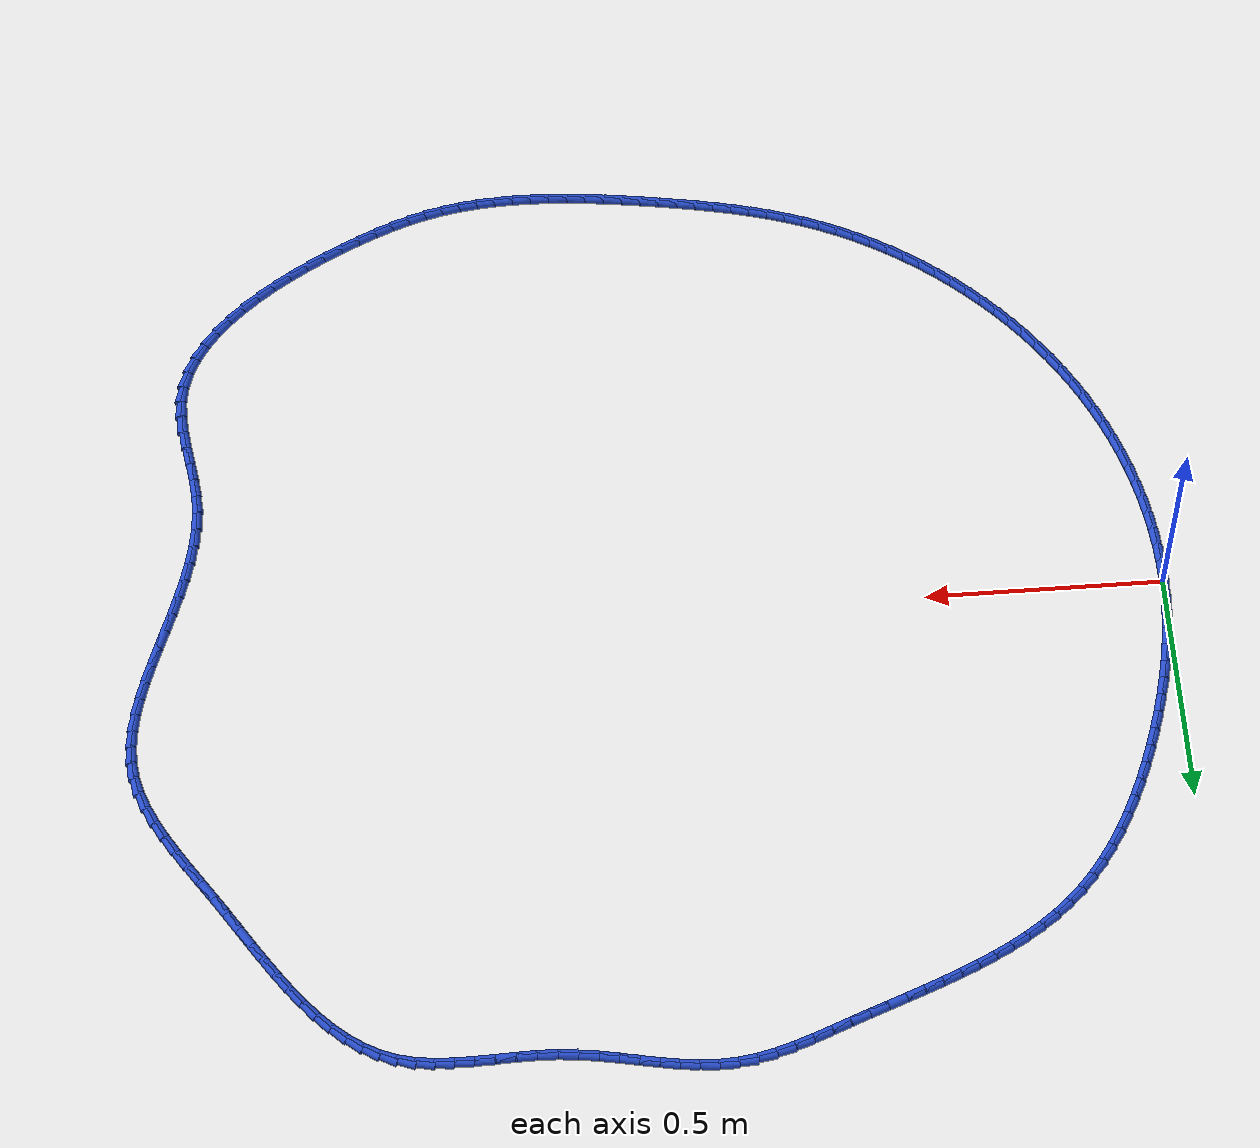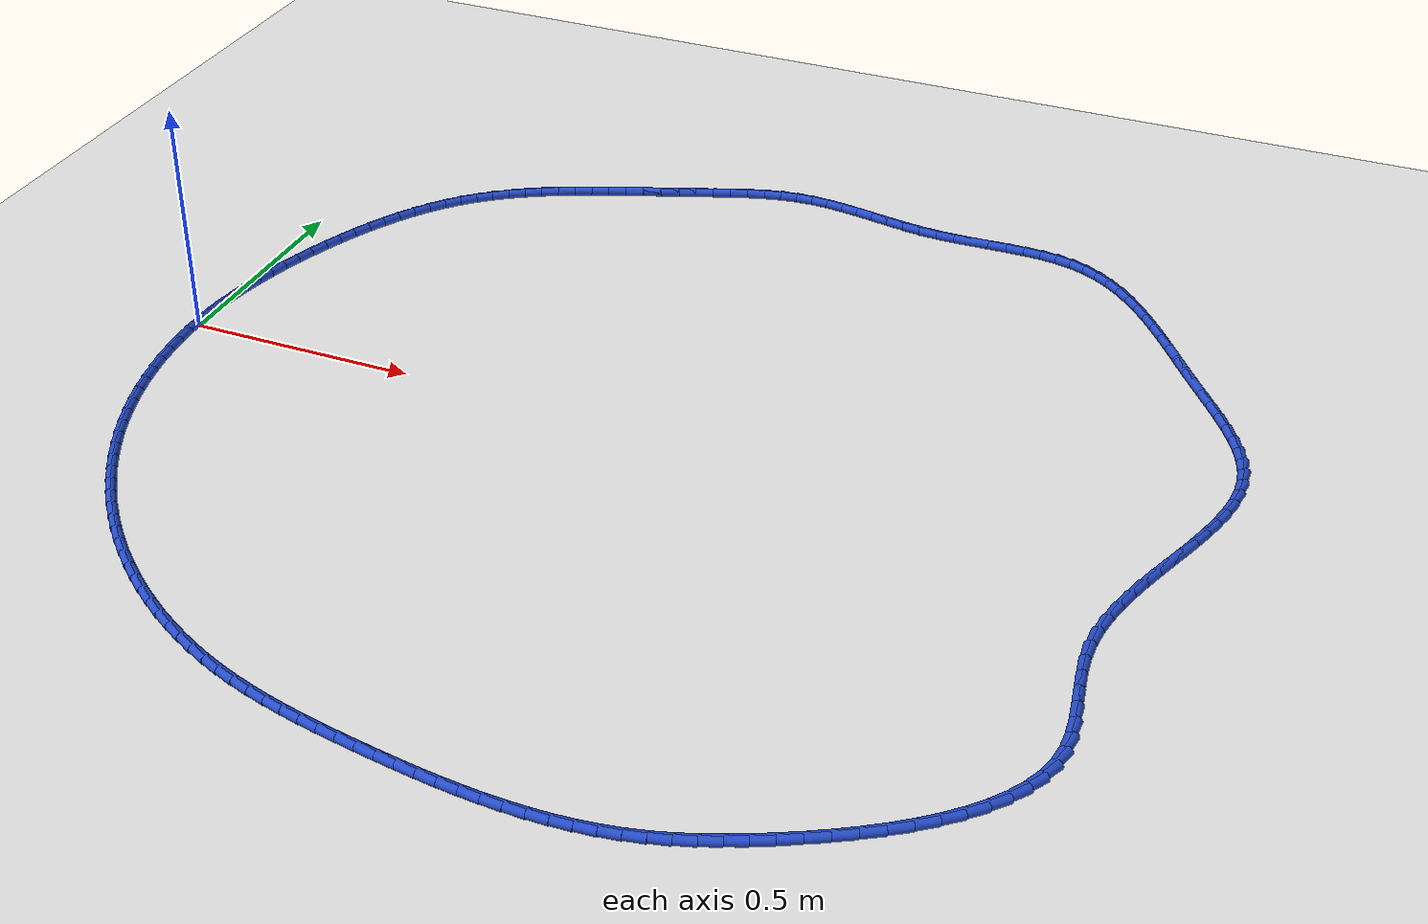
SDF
<sdf version="1.6">
 <world name="default">
  <light name="sun" type="directional">
   <pose>0 0 10 0 -0 0</pose>
   <diffuse>0.8 0.8 0.8 1</diffuse>
   <specular>0.2 0.2 0.2 1</specular>
   <attenuation>
    <range>1000</range>
    <constant>0.9</constant>
    <linear>0.01</linear>
    <quadratic>0.001</quadratic>
   </attenuation>
   <direction>-0.5 0.1 -0.9</direction>
  </light>
  <model name="ground_plane">
   <static>1</static>
   <link name="link">
    <collision name="collision">
     <geometry><plane><normal>0 0 1</normal><size>100 100</size></plane></geometry>
     <surface><friction><ode><mu>100</mu><mu2>50</mu2></ode></friction></surface>
    </collision>
    <visual name="visual">
     <cast_shadows>0</cast_shadows>
     <geometry><plane><normal>0 0 1</normal><size>100 100</size></plane></geometry>
     <material>
      <script><uri>file://media/materials/scripts/gazebo.material</uri><name>Gazebo/WhiteGlow</name></script>
     </material>
    </visual>
   </link>
  </model>
  <gravity>0 0 -9.8</gravity>
  <magnetic_field>6e-06 2.3e-05 -4.2e-05</magnetic_field>
  <atmosphere type="adiabatic"/>
  <physics name="default_physics" default="0" type="ode">
   <max_step_size>0.001</max_step_size>
   <real_time_factor>1</real_time_factor>
   <real_time_update_rate>1000</real_time_update_rate>
  </physics>
  <scene><ambient>0.4 0.4 0.4 1</ambient><background>0.7 0.7 0.7 1</background><shadows>1</shadows></scene>
  <spherical_coordinates>
   <surface_model>EARTH_WGS84</surface_model>
   <latitude_deg>0</latitude_deg>
   <longitude_deg>0</longitude_deg>
   <elevation>0</elevation>
   <heading_deg>0</heading_deg>
  </spherical_coordinates>
  <model name="line">
   <link name="link_0">
    <pose>0.0 -7.632783294297951e-17 0.01 0 1.57 1.5412899925752903</pose>
    <collision name="collision">
     <geometry><cylinder><radius>0.01</radius><length>0.08</length></cylinder></geometry>
    </collision>
    <visual name="visual">
     <material>
      <script><name>Gazebo/Blue</name><uri>file://media/materials/scripts/gazebo.material</uri></script>
     </material>
     <geometry><cylinder><radius>0.01</radius><length>0.08</length></cylinder></geometry>
    </visual>
   </link>
   <link name="link_1">
    <pose>0.0011664788379523727 0.03952169348541512 0.01 0 1.57 1.4992707240843812</pose>
    <collision name="collision">
     <geometry><cylinder><radius>0.01</radius><length>0.08</length></cylinder></geometry>
    </collision>
    <visual name="visual">
     <material>
      <script><name>Gazebo/Blue</name><uri>file://media/materials/scripts/gazebo.material</uri></script>
     </material>
     <geometry><cylinder><radius>0.01</radius><length>0.08</length></cylinder></geometry>
    </visual>
   </link>
   <link name="link_2">
    <pose>0.003988897844546765 0.0789146405587893 0.01 0 1.57 1.4590372391142037</pose>
    <collision name="collision">
     <geometry><cylinder><radius>0.01</radius><length>0.08</length></cylinder></geometry>
    </collision>
    <visual name="visual">
     <material>
      <script><name>Gazebo/Blue</name><uri>file://media/materials/scripts/gazebo.material</uri></script>
     </material>
     <geometry><cylinder><radius>0.01</radius><length>0.08</length></cylinder></geometry>
    </visual>
   </link>
   <link name="link_3">
    <pose>0.008395489492251475 0.11817972581189345 0.01 0 1.57 1.4207001486004143</pose>
    <collision name="collision">
     <geometry><cylinder><radius>0.01</radius><length>0.08</length></cylinder></geometry>
    </collision>
    <visual name="visual">
     <material>
      <script><name>Gazebo/Blue</name><uri>file://media/materials/scripts/gazebo.material</uri></script>
     </material>
     <geometry><cylinder><radius>0.01</radius><length>0.08</length></cylinder></geometry>
    </visual>
   </link>
   <link name="link_4">
    <pose>0.014314486253534816 0.15731783383649867 0.01 0 1.57 1.3843372284848252</pose>
    <collision name="collision">
     <geometry><cylinder><radius>0.01</radius><length>0.08</length></cylinder></geometry>
    </collision>
    <visual name="visual">
     <material>
      <script><name>Gazebo/Blue</name><uri>file://media/materials/scripts/gazebo.material</uri></script>
     </material>
     <geometry><cylinder><radius>0.01</radius><length>0.08</length></cylinder></geometry>
    </visual>
   </link>
   <link name="link_5">
    <pose>0.021674120600865095 0.19632984922437588 0.01 0 1.57 1.349996618190478</pose>
    <collision name="collision">
     <geometry><cylinder><radius>0.01</radius><length>0.08</length></cylinder></geometry>
    </collision>
    <visual name="visual">
     <material>
      <script><name>Gazebo/Blue</name><uri>file://media/materials/scripts/gazebo.material</uri></script>
     </material>
     <geometry><cylinder><radius>0.01</radius><length>0.08</length></cylinder></geometry>
    </visual>
   </link>
   <link name="link_6">
    <pose>0.03040262500671062 0.23521665656729615 0.01 0 1.57 1.3177006863759924</pose>
    <collision name="collision">
     <geometry><cylinder><radius>0.01</radius><length>0.08</length></cylinder></geometry>
    </collision>
    <visual name="visual">
     <material>
      <script><name>Gazebo/Blue</name><uri>file://media/materials/scripts/gazebo.material</uri></script>
     </material>
     <geometry><cylinder><radius>0.01</radius><length>0.08</length></cylinder></geometry>
    </visual>
   </link>
   <link name="link_7">
    <pose>0.04042823194353967 0.2739791404570303 0.01 0 1.57 1.2874501963512435</pose>
    <collision name="collision">
     <geometry><cylinder><radius>0.01</radius><length>0.08</length></cylinder></geometry>
    </collision>
    <visual name="visual">
     <material>
      <script><name>Gazebo/Blue</name><uri>file://media/materials/scripts/gazebo.material</uri></script>
     </material>
     <geometry><cylinder><radius>0.01</radius><length>0.08</length></cylinder></geometry>
    </visual>
   </link>
   <link name="link_8">
    <pose>0.0516791738838206 0.31261818548534964 0.01 0 1.57 1.259228476046142</pose>
    <collision name="collision">
     <geometry><cylinder><radius>0.01</radius><length>0.08</length></cylinder></geometry>
    </collision>
    <visual name="visual">
     <material>
      <script><name>Gazebo/Blue</name><uri>file://media/materials/scripts/gazebo.material</uri></script>
     </material>
     <geometry><cylinder><radius>0.01</radius><length>0.08</length></cylinder></geometry>
    </visual>
   </link>
   <link name="link_9">
    <pose>0.06408368330002168 0.35113467624402495 0.01 0 1.57 1.2326728110079732</pose>
    <collision name="collision">
     <geometry><cylinder><radius>0.01</radius><length>0.08</length></cylinder></geometry>
    </collision>
    <visual name="visual">
     <material>
      <script><name>Gazebo/Blue</name><uri>file://media/materials/scripts/gazebo.material</uri></script>
     </material>
     <geometry><cylinder><radius>0.01</radius><length>0.08</length></cylinder></geometry>
    </visual>
   </link>
   <link name="link_10">
    <pose>0.07757961715217083 0.38951606993776433 0.01 0 1.57 1.2046663298399918</pose>
    <collision name="collision">
     <geometry><cylinder><radius>0.01</radius><length>0.08</length></cylinder></geometry>
    </collision>
    <visual name="visual">
     <material>
      <script><name>Gazebo/Blue</name><uri>file://media/materials/scripts/gazebo.material</uri></script>
     </material>
     <geometry><cylinder><radius>0.01</radius><length>0.08</length></cylinder></geometry>
    </visual>
   </link>
   <link name="link_11">
    <pose>0.09219231562351649 0.4276277735226336 0.01 0 1.57 1.1733557439373374</pose>
    <collision name="collision">
     <geometry><cylinder><radius>0.01</radius><length>0.08</length></cylinder></geometry>
    </collision>
    <visual name="visual">
     <material>
      <script><name>Gazebo/Blue</name><uri>file://media/materials/scripts/gazebo.material</uri></script>
     </material>
     <geometry><cylinder><radius>0.01</radius><length>0.08</length></cylinder></geometry>
    </visual>
   </link>
   <link name="link_12">
    <pose>0.1079937880150481 0.46527008458613106 0.01 0 1.57 1.13842394764249</pose>
    <collision name="collision">
     <geometry><cylinder><radius>0.01</radius><length>0.08</length></cylinder></geometry>
    </collision>
    <visual name="visual">
     <material>
      <script><name>Gazebo/Blue</name><uri>file://media/materials/scripts/gazebo.material</uri></script>
     </material>
     <geometry><cylinder><radius>0.01</radius><length>0.08</length></cylinder></geometry>
    </visual>
   </link>
   <link name="link_13">
    <pose>0.1250564805326321 0.502242691177755 0.01 0 1.57 1.0995316928623047</pose>
    <collision name="collision">
     <geometry><cylinder><radius>0.01</radius><length>0.08</length></cylinder></geometry>
    </collision>
    <visual name="visual">
     <material>
      <script><name>Gazebo/Blue</name><uri>file://media/materials/scripts/gazebo.material</uri></script>
     </material>
     <geometry><cylinder><radius>0.01</radius><length>0.08</length></cylinder></geometry>
    </visual>
   </link>
   <link name="link_14">
    <pose>0.14345283938213488 0.5383452813470035 0.01 0 1.57 1.056309799792036</pose>
    <collision name="collision">
     <geometry><cylinder><radius>0.01</radius><length>0.08</length></cylinder></geometry>
    </collision>
    <visual name="visual">
     <material>
      <script><name>Gazebo/Blue</name><uri>file://media/materials/scripts/gazebo.material</uri></script>
     </material>
     <geometry><cylinder><radius>0.01</radius><length>0.08</length></cylinder></geometry>
    </visual>
   </link>
   <link name="link_15">
    <pose>0.16325531076942298 0.5733775431433752 0.01 0 1.57 1.0083719547693577</pose>
    <collision name="collision">
     <geometry><cylinder><radius>0.01</radius><length>0.08</length></cylinder></geometry>
    </collision>
    <visual name="visual">
     <material>
      <script><name>Gazebo/Blue</name><uri>file://media/materials/scripts/gazebo.material</uri></script>
     </material>
     <geometry><cylinder><radius>0.01</radius><length>0.08</length></cylinder></geometry>
    </visual>
   </link>
   <link name="link_16">
    <pose>0.18453634090036294 0.6071391646163686 0.01 0 1.57 0.9553355315662889</pose>
    <collision name="collision">
     <geometry><cylinder><radius>0.01</radius><length>0.08</length></cylinder></geometry>
    </collision>
    <visual name="visual">
     <material>
      <script><name>Gazebo/Blue</name><uri>file://media/materials/scripts/gazebo.material</uri></script>
     </material>
     <geometry><cylinder><radius>0.01</radius><length>0.08</length></cylinder></geometry>
    </visual>
   </link>
   <link name="link_17">
    <pose>0.20736837598082117 0.6394298338154821 0.01 0 1.57 0.8968532065829017</pose>
    <collision name="collision">
     <geometry><cylinder><radius>0.01</radius><length>0.08</length></cylinder></geometry>
    </collision>
    <visual name="visual">
     <material>
      <script><name>Gazebo/Blue</name><uri>file://media/materials/scripts/gazebo.material</uri></script>
     </material>
     <geometry><cylinder><radius>0.01</radius><length>0.08</length></cylinder></geometry>
    </visual>
   </link>
   <link name="link_18">
    <pose>0.231823862216664 0.6700492387902137 0.01 0 1.57 0.832657710094816</pose>
    <collision name="collision">
     <geometry><cylinder><radius>0.01</radius><length>0.08</length></cylinder></geometry>
    </collision>
    <visual name="visual">
     <material>
      <script><name>Gazebo/Blue</name><uri>file://media/materials/scripts/gazebo.material</uri></script>
     </material>
     <geometry><cylinder><radius>0.01</radius><length>0.08</length></cylinder></geometry>
    </visual>
   </link>
   <link name="link_19">
    <pose>0.25797524581375797 0.6987970675900622 0.01 0 1.57 0.7628251900576954</pose>
    <collision name="collision">
     <geometry><cylinder><radius>0.01</radius><length>0.08</length></cylinder></geometry>
    </collision>
    <visual name="visual">
     <material>
      <script><name>Gazebo/Blue</name><uri>file://media/materials/scripts/gazebo.material</uri></script>
     </material>
     <geometry><cylinder><radius>0.01</radius><length>0.08</length></cylinder></geometry>
    </visual>
   </link>
   <link name="link_20">
    <pose>0.2858909137905333 0.7254800718240572 0.01 0 1.57 0.6928456704834146</pose>
    <collision name="collision">
     <geometry><cylinder><radius>0.01</radius><length>0.08</length></cylinder></geometry>
    </collision>
    <visual name="visual">
     <material>
      <script><name>Gazebo/Blue</name><uri>file://media/materials/scripts/gazebo.material</uri></script>
     </material>
     <geometry><cylinder><radius>0.01</radius><length>0.08</length></cylinder></geometry>
    </visual>
   </link>
   <link name="link_21">
    <pose>0.31553416655634947 0.7500878686453204 0.01 0 1.57 0.6290100344715495</pose>
    <collision name="collision">
     <geometry><cylinder><radius>0.01</radius><length>0.08</length></cylinder></geometry>
    </collision>
    <visual name="visual">
     <material>
      <script><name>Gazebo/Blue</name><uri>file://media/materials/scripts/gazebo.material</uri></script>
     </material>
     <geometry><cylinder><radius>0.01</radius><length>0.08</length></cylinder></geometry>
    </visual>
   </link>
   <link name="link_22">
    <pose>0.3467562590621506 0.7728050501319181 0.01 0 1.57 0.5720623573704425</pose>
    <collision name="collision">
     <geometry><cylinder><radius>0.01</radius><length>0.08</length></cylinder></geometry>
    </collision>
    <visual name="visual">
     <material>
      <script><name>Gazebo/Blue</name><uri>file://media/materials/scripts/gazebo.material</uri></script>
     </material>
     <geometry><cylinder><radius>0.01</radius><length>0.08</length></cylinder></geometry>
    </visual>
   </link>
   <link name="link_23">
    <pose>0.379402993507576 0.79382569691943 0.01 0 1.57 0.5221846340085324</pose>
    <collision name="collision">
     <geometry><cylinder><radius>0.01</radius><length>0.08</length></cylinder></geometry>
    </collision>
    <visual name="visual">
     <material>
      <script><name>Gazebo/Blue</name><uri>file://media/materials/scripts/gazebo.material</uri></script>
     </material>
     <geometry><cylinder><radius>0.01</radius><length>0.08</length></cylinder></geometry>
    </visual>
   </link>
   <link name="link_24">
    <pose>0.4133201720922656 0.813343889643436 0.01 0 1.57 0.4793493766203029</pose>
    <collision name="collision">
     <geometry><cylinder><radius>0.01</radius><length>0.08</length></cylinder></geometry>
    </collision>
    <visual name="visual">
     <material>
      <script><name>Gazebo/Blue</name><uri>file://media/materials/scripts/gazebo.material</uri></script>
     </material>
     <geometry><cylinder><radius>0.01</radius><length>0.08</length></cylinder></geometry>
    </visual>
   </link>
   <link name="link_25">
    <pose>0.44835359701585875 0.831553708939516 0.01 0 1.57 0.443395670748436</pose>
    <collision name="collision">
     <geometry><cylinder><radius>0.01</radius><length>0.08</length></cylinder></geometry>
    </collision>
    <visual name="visual">
     <material>
      <script><name>Gazebo/Blue</name><uri>file://media/materials/scripts/gazebo.material</uri></script>
     </material>
     <geometry><cylinder><radius>0.01</radius><length>0.08</length></cylinder></geometry>
    </visual>
   </link>
   <link name="link_26">
    <pose>0.4843490704779951 0.8486492354432495 0.01 0 1.57 0.4140936662736246</pose>
    <collision name="collision">
     <geometry><cylinder><radius>0.01</radius><length>0.08</length></cylinder></geometry>
    </collision>
    <visual name="visual">
     <material>
      <script><name>Gazebo/Blue</name><uri>file://media/materials/scripts/gazebo.material</uri></script>
     </material>
     <geometry><cylinder><radius>0.01</radius><length>0.08</length></cylinder></geometry>
    </visual>
   </link>
   <link name="link_27">
    <pose>0.5211523946783141 0.8648245497902166 0.01 0 1.57 0.39119404927412676</pose>
    <collision name="collision">
     <geometry><cylinder><radius>0.01</radius><length>0.08</length></cylinder></geometry>
    </collision>
    <visual name="visual">
     <material>
      <script><name>Gazebo/Blue</name><uri>file://media/materials/scripts/gazebo.material</uri></script>
     </material>
     <geometry><cylinder><radius>0.01</radius><length>0.08</length></cylinder></geometry>
    </visual>
   </link>
   <link name="link_28">
    <pose>0.5586093718164556 0.8802737326159972 0.01 0 1.57 0.3744631647613453</pose>
    <collision name="collision">
     <geometry><cylinder><radius>0.01</radius><length>0.08</length></cylinder></geometry>
    </collision>
    <visual name="visual">
     <material>
      <script><name>Gazebo/Blue</name><uri>file://media/materials/scripts/gazebo.material</uri></script>
     </material>
     <geometry><cylinder><radius>0.01</radius><length>0.08</length></cylinder></geometry>
    </visual>
   </link>
   <link name="link_29">
    <pose>0.5965658040920592 0.8951908645561709 0.01 0 1.57 0.36370628559066215</pose>
    <collision name="collision">
     <geometry><cylinder><radius>0.01</radius><length>0.08</length></cylinder></geometry>
    </collision>
    <visual name="visual">
     <material>
      <script><name>Gazebo/Blue</name><uri>file://media/materials/scripts/gazebo.material</uri></script>
     </material>
     <geometry><cylinder><radius>0.01</radius><length>0.08</length></cylinder></geometry>
    </visual>
   </link>
   <link name="link_30">
    <pose>0.634867493704764 0.9097700262463174 0.01 0 1.57 0.35878185655316497</pose>
    <collision name="collision">
     <geometry><cylinder><radius>0.01</radius><length>0.08</length></cylinder></geometry>
    </collision>
    <visual name="visual">
     <material>
      <script><name>Gazebo/Blue</name><uri>file://media/materials/scripts/gazebo.material</uri></script>
     </material>
     <geometry><cylinder><radius>0.01</radius><length>0.08</length></cylinder></geometry>
    </visual>
   </link>
   <link name="link_31">
    <pose>0.6733602428542103 0.9242052983220168 0.01 0 1.57 0.359609105543254</pose>
    <collision name="collision">
     <geometry><cylinder><radius>0.01</radius><length>0.08</length></cylinder></geometry>
    </collision>
    <visual name="visual">
     <material>
      <script><name>Gazebo/Blue</name><uri>file://media/materials/scripts/gazebo.material</uri></script>
     </material>
     <geometry><cylinder><radius>0.01</radius><length>0.08</length></cylinder></geometry>
    </visual>
   </link>
   <link name="link_32">
    <pose>0.7118898537400373 0.9386907614188489 0.01 0 1.57 0.36610900160165105</pose>
    <collision name="collision">
     <geometry><cylinder><radius>0.01</radius><length>0.08</length></cylinder></geometry>
    </collision>
    <visual name="visual">
     <material>
      <script><name>Gazebo/Blue</name><uri>file://media/materials/scripts/gazebo.material</uri></script>
     </material>
     <geometry><cylinder><radius>0.01</radius><length>0.08</length></cylinder></geometry>
    </visual>
   </link>
   <link name="link_33">
    <pose>0.7503027326218837 0.9534180107579484 0.01 0 1.57 0.37126597722281707</pose>
    <collision name="collision">
     <geometry><cylinder><radius>0.01</radius><length>0.08</length></cylinder></geometry>
    </collision>
    <visual name="visual">
     <material>
      <script><name>Gazebo/Blue</name><uri>file://media/materials/scripts/gazebo.material</uri></script>
     </material>
     <geometry><cylinder><radius>0.01</radius><length>0.08</length></cylinder></geometry>
    </visual>
   </link>
   <link name="link_34">
    <pose>0.7885143291995406 0.9682945612311419 0.01 0 1.57 0.36150294382758663</pose>
    <collision name="collision">
     <geometry><cylinder><radius>0.01</radius><length>0.08</length></cylinder></geometry>
    </collision>
    <visual name="visual">
     <material>
      <script><name>Gazebo/Blue</name><uri>file://media/materials/scripts/gazebo.material</uri></script>
     </material>
     <geometry><cylinder><radius>0.01</radius><length>0.08</length></cylinder></geometry>
    </visual>
   </link>
   <link name="link_35">
    <pose>0.8265720620033965 0.9826849398841684 0.01 0 1.57 0.3347821961690057</pose>
    <collision name="collision">
     <geometry><cylinder><radius>0.01</radius><length>0.08</length></cylinder></geometry>
    </collision>
    <visual name="visual">
     <material>
      <script><name>Gazebo/Blue</name><uri>file://media/materials/scripts/gazebo.material</uri></script>
     </material>
     <geometry><cylinder><radius>0.01</radius><length>0.08</length></cylinder></geometry>
    </visual>
   </link>
   <link name="link_36">
    <pose>0.8645382196826192 0.9958924904232626 0.01 0 1.57 0.29017471325000943</pose>
    <collision name="collision">
     <geometry><cylinder><radius>0.01</radius><length>0.08</length></cylinder></geometry>
    </collision>
    <visual name="visual">
     <material>
      <script><name>Gazebo/Blue</name><uri>file://media/materials/scripts/gazebo.material</uri></script>
     </material>
     <geometry><cylinder><radius>0.01</radius><length>0.08</length></cylinder></geometry>
    </visual>
   </link>
   <link name="link_37">
    <pose>0.902475090886375 1.0072205565546581 0.01 0 1.57 0.2265399543691088</pose>
    <collision name="collision">
     <geometry><cylinder><radius>0.01</radius><length>0.08</length></cylinder></geometry>
    </collision>
    <visual name="visual">
     <material>
      <script><name>Gazebo/Blue</name><uri>file://media/materials/scripts/gazebo.material</uri></script>
     </material>
     <geometry><cylinder><radius>0.01</radius><length>0.08</length></cylinder></geometry>
    </visual>
   </link>
   <link name="link_38">
    <pose>0.9404449642638316 1.01597248198459 0.01 0 1.57 0.14295883201085677</pose>
    <collision name="collision">
     <geometry><cylinder><radius>0.01</radius><length>0.08</length></cylinder></geometry>
    </collision>
    <visual name="visual">
     <material>
      <script><name>Gazebo/Blue</name><uri>file://media/materials/scripts/gazebo.material</uri></script>
     </material>
     <geometry><cylinder><radius>0.01</radius><length>0.08</length></cylinder></geometry>
    </visual>
   </link>
   <link name="link_39">
    <pose>0.9785101284641564 1.0214516104192926 0.01 0 1.57 0.04289458394852147</pose>
    <collision name="collision">
     <geometry><cylinder><radius>0.01</radius><length>0.08</length></cylinder></geometry>
    </collision>
    <visual name="visual">
     <material>
      <script><name>Gazebo/Blue</name><uri>file://media/materials/scripts/gazebo.material</uri></script>
     </material>
     <geometry><cylinder><radius>0.01</radius><length>0.08</length></cylinder></geometry>
    </visual>
   </link>
   <link name="link_40">
    <pose>1.0167306579591828 1.023092070372587 0.01 0 1.57 -0.0473076465144964</pose>
    <collision name="collision">
     <geometry><cylinder><radius>0.01</radius><length>0.08</length></cylinder></geometry>
    </collision>
    <visual name="visual">
     <material>
      <script><name>Gazebo/Blue</name><uri>file://media/materials/scripts/gazebo.material</uri></script>
     </material>
     <geometry><cylinder><radius>0.01</radius><length>0.08</length></cylinder></geometry>
    </visual>
   </link>
   <link name="link_41">
    <pose>1.055150625651718 1.02127315500039 0.01 0 1.57 -0.11547012662469658</pose>
    <collision name="collision">
     <geometry><cylinder><radius>0.01</radius><length>0.08</length></cylinder></geometry>
    </collision>
    <visual name="visual">
     <material>
      <script><name>Gazebo/Blue</name><uri>file://media/materials/scripts/gazebo.material</uri></script>
     </material>
     <geometry><cylinder><radius>0.01</radius><length>0.08</length></cylinder></geometry>
    </visual>
   </link>
   <link name="link_42">
    <pose>1.0938070719578519 1.0167895453357794 0.01 0 1.57 -0.16173549665649767</pose>
    <collision name="collision">
     <geometry><cylinder><radius>0.01</radius><length>0.08</length></cylinder></geometry>
    </collision>
    <visual name="visual">
     <material>
      <script><name>Gazebo/Blue</name><uri>file://media/materials/scripts/gazebo.material</uri></script>
     </material>
     <geometry><cylinder><radius>0.01</radius><length>0.08</length></cylinder></geometry>
    </visual>
   </link>
   <link name="link_43">
    <pose>1.1327370070030243 1.010437711589605 0.01 0 1.57 -0.18697242384630391</pose>
    <collision name="collision">
     <geometry><cylinder><radius>0.01</radius><length>0.08</length></cylinder></geometry>
    </collision>
    <visual name="visual">
     <material>
      <script><name>Gazebo/Blue</name><uri>file://media/materials/scripts/gazebo.material</uri></script>
     </material>
     <geometry><cylinder><radius>0.01</radius><length>0.08</length></cylinder></geometry>
    </visual>
   </link>
   <link name="link_44">
    <pose>1.171977440912676 1.0030141239727182 0.01 0 1.57 -0.19207760746956504</pose>
    <collision name="collision">
     <geometry><cylinder><radius>0.01</radius><length>0.08</length></cylinder></geometry>
    </collision>
    <visual name="visual">
     <material>
      <script><name>Gazebo/Blue</name><uri>file://media/materials/scripts/gazebo.material</uri></script>
     </material>
     <geometry><cylinder><radius>0.01</radius><length>0.08</length></cylinder></geometry>
    </visual>
   </link>
   <link name="link_45">
    <pose>1.2115653838122473 0.9953152526959689 0.01 0 1.57 -0.1776722749751937</pose>
    <collision name="collision">
     <geometry><cylinder><radius>0.01</radius><length>0.08</length></cylinder></geometry>
    </collision>
    <visual name="visual">
     <material>
      <script><name>Gazebo/Blue</name><uri>file://media/materials/scripts/gazebo.material</uri></script>
     </material>
     <geometry><cylinder><radius>0.01</radius><length>0.08</length></cylinder></geometry>
    </visual>
   </link>
   <link name="link_46">
    <pose>1.2515378458271778 0.9881375679702079 0.01 0 1.57 -0.14406671686101993</pose>
    <collision name="collision">
     <geometry><cylinder><radius>0.01</radius><length>0.08</length></cylinder></geometry>
    </collision>
    <visual name="visual">
     <material>
      <script><name>Gazebo/Blue</name><uri>file://media/materials/scripts/gazebo.material</uri></script>
     </material>
     <geometry><cylinder><radius>0.01</radius><length>0.08</length></cylinder></geometry>
    </visual>
   </link>
   <link name="link_47">
    <pose>1.2919318370829087 0.982277540006286 0.01 0 1.57 -0.09146678892255376</pose>
    <collision name="collision">
     <geometry><cylinder><radius>0.01</radius><length>0.08</length></cylinder></geometry>
    </collision>
    <visual name="visual">
     <material>
      <script><name>Gazebo/Blue</name><uri>file://media/materials/scripts/gazebo.material</uri></script>
     </material>
     <geometry><cylinder><radius>0.01</radius><length>0.08</length></cylinder></geometry>
    </visual>
   </link>
   <link name="link_48">
    <pose>1.3327841298732073 0.9785304565483715 0.01 0 1.57 -0.031044724939890685</pose>
    <collision name="collision">
     <geometry><cylinder><radius>0.01</radius><length>0.08</length></cylinder></geometry>
    </collision>
    <visual name="visual">
     <material>
      <script><name>Gazebo/Blue</name><uri>file://media/materials/scripts/gazebo.material</uri></script>
     </material>
     <geometry><cylinder><radius>0.01</radius><length>0.08</length></cylinder></geometry>
    </visual>
   </link>
   <link name="link_49">
    <pose>1.3740425126423634 0.9772491897597785 0.01 0 1.57 0.010476320669949028</pose>
    <collision name="collision">
     <geometry><cylinder><radius>0.01</radius><length>0.08</length></cylinder></geometry>
    </collision>
    <visual name="visual">
     <material>
      <script><name>Gazebo/Blue</name><uri>file://media/materials/scripts/gazebo.material</uri></script>
     </material>
     <geometry><cylinder><radius>0.01</radius><length>0.08</length></cylinder></geometry>
    </visual>
   </link>
   <link name="link_50">
    <pose>1.4154327668275317 0.977682823199582 0.01 0 1.57 0.02979491065720952</pose>
    <collision name="collision">
     <geometry><cylinder><radius>0.01</radius><length>0.08</length></cylinder></geometry>
    </collision>
    <visual name="visual">
     <material>
      <script><name>Gazebo/Blue</name><uri>file://media/materials/scripts/gazebo.material</uri></script>
     </material>
     <geometry><cylinder><radius>0.01</radius><length>0.08</length></cylinder></geometry>
    </visual>
   </link>
   <link name="link_51">
    <pose>1.456646624153628 0.9789111498948614 0.01 0 1.57 0.02707010692603462</pose>
    <collision name="collision">
     <geometry><cylinder><radius>0.01</radius><length>0.08</length></cylinder></geometry>
    </collision>
    <visual name="visual">
     <material>
      <script><name>Gazebo/Blue</name><uri>file://media/materials/scripts/gazebo.material</uri></script>
     </material>
     <geometry><cylinder><radius>0.01</radius><length>0.08</length></cylinder></geometry>
    </visual>
   </link>
   <link name="link_52">
    <pose>1.4973758163455697 0.9800139628726963 0.01 0 1.57 0.0014295843004920234</pose>
    <collision name="collision">
     <geometry><cylinder><radius>0.01</radius><length>0.08</length></cylinder></geometry>
    </collision>
    <visual name="visual">
     <material>
      <script><name>Gazebo/Blue</name><uri>file://media/materials/scripts/gazebo.material</uri></script>
     </material>
     <geometry><cylinder><radius>0.01</radius><length>0.08</length></cylinder></geometry>
    </visual>
   </link>
   <link name="link_53">
    <pose>1.5373120751282734 0.9800710551601658 0.01 0 1.57 -0.049112851169080055</pose>
    <collision name="collision">
     <geometry><cylinder><radius>0.01</radius><length>0.08</length></cylinder></geometry>
    </collision>
    <visual name="visual">
     <material>
      <script><name>Gazebo/Blue</name><uri>file://media/materials/scripts/gazebo.material</uri></script>
     </material>
     <geometry><cylinder><radius>0.01</radius><length>0.08</length></cylinder></geometry>
    </visual>
   </link>
   <link name="link_54">
    <pose>1.5761471322266551 0.9781622197843488 0.01 0 1.57 -0.12742590527282288</pose>
    <collision name="collision">
     <geometry><cylinder><radius>0.01</radius><length>0.08</length></cylinder></geometry>
    </collision>
    <visual name="visual">
     <material>
      <script><name>Gazebo/Blue</name><uri>file://media/materials/scripts/gazebo.material</uri></script>
     </material>
     <geometry><cylinder><radius>0.01</radius><length>0.08</length></cylinder></geometry>
    </visual>
   </link>
   <link name="link_55">
    <pose>1.6135727193656337 0.9733672497723256 0.01 0 1.57 -0.23637345175117339</pose>
    <collision name="collision">
     <geometry><cylinder><radius>0.01</radius><length>0.08</length></cylinder></geometry>
    </collision>
    <visual name="visual">
     <material>
      <script><name>Gazebo/Blue</name><uri>file://media/materials/scripts/gazebo.material</uri></script>
     </material>
     <geometry><cylinder><radius>0.01</radius><length>0.08</length></cylinder></geometry>
    </visual>
   </link>
   <link name="link_56">
    <pose>1.6492806139703906 0.9647660619033969 0.01 0 1.57 -0.3685137428374353</pose>
    <collision name="collision">
     <geometry><cylinder><radius>0.01</radius><length>0.08</length></cylinder></geometry>
    </collision>
    <visual name="visual">
     <material>
      <script><name>Gazebo/Blue</name><uri>file://media/materials/scripts/gazebo.material</uri></script>
     </material>
     <geometry><cylinder><radius>0.01</radius><length>0.08</length></cylinder></geometry>
    </visual>
   </link>
   <link name="link_57">
    <pose>1.6830663559299277 0.9517195523998742 0.01 0 1.57 -0.4946535043019818</pose>
    <collision name="collision">
     <geometry><cylinder><radius>0.01</radius><length>0.08</length></cylinder></geometry>
    </collision>
    <visual name="visual">
     <material>
      <script><name>Gazebo/Blue</name><uri>file://media/materials/scripts/gazebo.material</uri></script>
     </material>
     <geometry><cylinder><radius>0.01</radius><length>0.08</length></cylinder></geometry>
    </visual>
   </link>
   <link name="link_58">
    <pose>1.715050253666191 0.9344680615348027 0.01 0 1.57 -0.6060366607881206</pose>
    <collision name="collision">
     <geometry><cylinder><radius>0.01</radius><length>0.08</length></cylinder></geometry>
    </collision>
    <visual name="visual">
     <material>
      <script><name>Gazebo/Blue</name><uri>file://media/materials/scripts/gazebo.material</uri></script>
     </material>
     <geometry><cylinder><radius>0.01</radius><length>0.08</length></cylinder></geometry>
    </visual>
   </link>
   <link name="link_59">
    <pose>1.7454159838278123 0.9134235250540369 0.01 0 1.57 -0.701155440004282</pose>
    <collision name="collision">
     <geometry><cylinder><radius>0.01</radius><length>0.08</length></cylinder></geometry>
    </collision>
    <visual name="visual">
     <material>
      <script><name>Gazebo/Blue</name><uri>file://media/materials/scripts/gazebo.material</uri></script>
     </material>
     <geometry><cylinder><radius>0.01</radius><length>0.08</length></cylinder></geometry>
    </visual>
   </link>
   <link name="link_60">
    <pose>1.774347223063422 0.8889978787034305 0.01 0 1.57 -0.7802124956566824</pose>
    <collision name="collision">
     <geometry><cylinder><radius>0.01</radius><length>0.08</length></cylinder></geometry>
    </collision>
    <visual name="visual">
     <material>
      <script><name>Gazebo/Blue</name><uri>file://media/materials/scripts/gazebo.material</uri></script>
     </material>
     <geometry><cylinder><radius>0.01</radius><length>0.08</length></cylinder></geometry>
    </visual>
   </link>
   <link name="link_61">
    <pose>1.8020276480216533 0.8616030582288373 0.01 0 1.57 -0.8443547942164572</pose>
    <collision name="collision">
     <geometry><cylinder><radius>0.01</radius><length>0.08</length></cylinder></geometry>
    </collision>
    <visual name="visual">
     <material>
      <script><name>Gazebo/Blue</name><uri>file://media/materials/scripts/gazebo.material</uri></script>
     </material>
     <geometry><cylinder><radius>0.01</radius><length>0.08</length></cylinder></geometry>
    </visual>
   </link>
   <link name="link_62">
    <pose>1.8286409353511361 0.8316509993761118 0.01 0 1.57 -0.8950695087315674</pose>
    <collision name="collision">
     <geometry><cylinder><radius>0.01</radius><length>0.08</length></cylinder></geometry>
    </collision>
    <visual name="visual">
     <material>
      <script><name>Gazebo/Blue</name><uri>file://media/materials/scripts/gazebo.material</uri></script>
     </material>
     <geometry><cylinder><radius>0.01</radius><length>0.08</length></cylinder></geometry>
    </visual>
   </link>
   <link name="link_63">
    <pose>1.854370761700503 0.799553637891107 0.01 0 1.57 -0.9338157150253733</pose>
    <collision name="collision">
     <geometry><cylinder><radius>0.01</radius><length>0.08</length></cylinder></geometry>
    </collision>
    <visual name="visual">
     <material>
      <script><name>Gazebo/Blue</name><uri>file://media/materials/scripts/gazebo.material</uri></script>
     </material>
     <geometry><cylinder><radius>0.01</radius><length>0.08</length></cylinder></geometry>
    </visual>
   </link>
   <link name="link_64">
    <pose>1.8794008037183847 0.7657229095196778 0.01 0 1.57 -0.9618400783355507</pose>
    <collision name="collision">
     <geometry><cylinder><radius>0.01</radius><length>0.08</length></cylinder></geometry>
    </collision>
    <visual name="visual">
     <material>
      <script><name>Gazebo/Blue</name><uri>file://media/materials/scripts/gazebo.material</uri></script>
     </material>
     <geometry><cylinder><radius>0.01</radius><length>0.08</length></cylinder></geometry>
    </visual>
   </link>
   <link name="link_65">
    <pose>1.9039147380534125 0.7305707500076776 0.01 0 1.57 -0.9801031800926108</pose>
    <collision name="collision">
     <geometry><cylinder><radius>0.01</radius><length>0.08</length></cylinder></geometry>
    </collision>
    <visual name="visual">
     <material>
      <script><name>Gazebo/Blue</name><uri>file://media/materials/scripts/gazebo.material</uri></script>
     </material>
     <geometry><cylinder><radius>0.01</radius><length>0.08</length></cylinder></geometry>
    </visual>
   </link>
   <link name="link_66">
    <pose>1.9280962413542189 0.6945090951009601 0.01 0 1.57 -0.989260997402861</pose>
    <collision name="collision">
     <geometry><cylinder><radius>0.01</radius><length>0.08</length></cylinder></geometry>
    </collision>
    <visual name="visual">
     <material>
      <script><name>Gazebo/Blue</name><uri>file://media/materials/scripts/gazebo.material</uri></script>
     </material>
     <geometry><cylinder><radius>0.01</radius><length>0.08</length></cylinder></geometry>
    </visual>
   </link>
   <link name="link_67">
    <pose>1.9521289902694339 0.6579498805453801 0.01 0 1.57 -0.9896681917891645</pose>
    <collision name="collision">
     <geometry><cylinder><radius>0.01</radius><length>0.08</length></cylinder></geometry>
    </collision>
    <visual name="visual">
     <material>
      <script><name>Gazebo/Blue</name><uri>file://media/materials/scripts/gazebo.material</uri></script>
     </material>
     <geometry><cylinder><radius>0.01</radius><length>0.08</length></cylinder></geometry>
    </visual>
   </link>
   <link name="link_68">
    <pose>1.9761966614476907 0.6213050420867908 0.01 0 1.57 -0.9814410797622237</pose>
    <collision name="collision">
     <geometry><cylinder><radius>0.01</radius><length>0.08</length></cylinder></geometry>
    </collision>
    <visual name="visual">
     <material>
      <script><name>Gazebo/Blue</name><uri>file://media/materials/scripts/gazebo.material</uri></script>
     </material>
     <geometry><cylinder><radius>0.01</radius><length>0.08</length></cylinder></geometry>
    </visual>
   </link>
   <link name="link_69">
    <pose>2.0004809611432925 0.5849851324418796 0.01 0 1.57 -0.9712053492613443</pose>
    <collision name="collision">
     <geometry><cylinder><radius>0.01</radius><length>0.08</length></cylinder></geometry>
    </collision>
    <visual name="visual">
     <material>
      <script><name>Gazebo/Blue</name><uri>file://media/materials/scripts/gazebo.material</uri></script>
     </material>
     <geometry><cylinder><radius>0.01</radius><length>0.08</length></cylinder></geometry>
    </visual>
   </link>
   <link name="link_70">
    <pose>2.024920735771882 0.549230239849291 0.01 0 1.57 -0.9723051321614041</pose>
    <collision name="collision">
     <geometry><cylinder><radius>0.01</radius><length>0.08</length></cylinder></geometry>
    </collision>
    <visual name="visual">
     <material>
      <script><name>Gazebo/Blue</name><uri>file://media/materials/scripts/gazebo.material</uri></script>
     </material>
     <geometry><cylinder><radius>0.01</radius><length>0.08</length></cylinder></geometry>
    </visual>
   </link>
   <link name="link_71">
    <pose>2.0489807535324855 0.5139476947883321 0.01 0 1.57 -0.9868465801911364</pose>
    <collision name="collision">
     <geometry><cylinder><radius>0.01</radius><length>0.08</length></cylinder></geometry>
    </collision>
    <visual name="visual">
     <material>
      <script><name>Gazebo/Blue</name><uri>file://media/materials/scripts/gazebo.material</uri></script>
     </material>
     <geometry><cylinder><radius>0.01</radius><length>0.08</length></cylinder></geometry>
    </visual>
   </link>
   <link name="link_72">
    <pose>2.0720709764454135 0.47900635902030775 0.01 0 1.57 -1.015862871302016</pose>
    <collision name="collision">
     <geometry><cylinder><radius>0.01</radius><length>0.08</length></cylinder></geometry>
    </collision>
    <visual name="visual">
     <material>
      <script><name>Gazebo/Blue</name><uri>file://media/materials/scripts/gazebo.material</uri></script>
     </material>
     <geometry><cylinder><radius>0.01</radius><length>0.08</length></cylinder></geometry>
    </visual>
   </link>
   <link name="link_73">
    <pose>2.093601366530979 0.4442750943065223 0.01 0 1.57 -1.0608527000063255</pose>
    <collision name="collision">
     <geometry><cylinder><radius>0.01</radius><length>0.08</length></cylinder></geometry>
    </collision>
    <visual name="visual">
     <material>
      <script><name>Gazebo/Blue</name><uri>file://media/materials/scripts/gazebo.material</uri></script>
     </material>
     <geometry><cylinder><radius>0.01</radius><length>0.08</length></cylinder></geometry>
    </visual>
   </link>
   <link name="link_74">
    <pose>2.112981885809495 0.4096227624082796 0.01 0 1.57 -1.1236878434630777</pose>
    <collision name="collision">
     <geometry><cylinder><radius>0.01</radius><length>0.08</length></cylinder></geometry>
    </collision>
    <visual name="visual">
     <material>
      <script><name>Gazebo/Blue</name><uri>file://media/materials/scripts/gazebo.material</uri></script>
     </material>
     <geometry><cylinder><radius>0.01</radius><length>0.08</length></cylinder></geometry>
    </visual>
   </link>
   <link name="link_75">
    <pose>2.1296224963012733 0.3749182250868848 0.01 0 1.57 -1.2063157913586733</pose>
    <collision name="collision">
     <geometry><cylinder><radius>0.01</radius><length>0.08</length></cylinder></geometry>
    </collision>
    <visual name="visual">
     <material>
      <script><name>Gazebo/Blue</name><uri>file://media/materials/scripts/gazebo.material</uri></script>
     </material>
     <geometry><cylinder><radius>0.01</radius><length>0.08</length></cylinder></geometry>
    </visual>
   </link>
   <link name="link_76">
    <pose>2.142933160026626 0.3400303441036419 0.01 0 1.57 -1.3101042368183262</pose>
    <collision name="collision">
     <geometry><cylinder><radius>0.01</radius><length>0.08</length></cylinder></geometry>
    </collision>
    <visual name="visual">
     <material>
      <script><name>Gazebo/Blue</name><uri>file://media/materials/scripts/gazebo.material</uri></script>
     </material>
     <geometry><cylinder><radius>0.01</radius><length>0.08</length></cylinder></geometry>
    </visual>
   </link>
   <link name="link_77">
    <pose>2.152323839005867 0.30482798121985527 0.01 0 1.57 -1.4335977611330513</pose>
    <collision name="collision">
     <geometry><cylinder><radius>0.01</radius><length>0.08</length></cylinder></geometry>
    </collision>
    <visual name="visual">
     <material>
      <script><name>Gazebo/Blue</name><uri>file://media/materials/scripts/gazebo.material</uri></script>
     </material>
     <geometry><cylinder><radius>0.01</radius><length>0.08</length></cylinder></geometry>
    </visual>
   </link>
   <link name="link_78">
    <pose>2.1572448606391506 0.2691854369229246 0.01 0 1.57 -1.5565648857223602</pose>
    <collision name="collision">
     <geometry><cylinder><radius>0.01</radius><length>0.08</length></cylinder></geometry>
    </collision>
    <visual name="visual">
     <material>
      <script><name>Gazebo/Blue</name><uri>file://media/materials/scripts/gazebo.material</uri></script>
     </material>
     <geometry><cylinder><radius>0.01</radius><length>0.08</length></cylinder></geometry>
    </visual>
   </link>
   <link name="link_79">
    <pose>2.157759019011677 0.23305953386541228 0.01 0 1.57 1.479381670420758</pose>
    <collision name="collision">
     <geometry><cylinder><radius>0.01</radius><length>0.08</length></cylinder></geometry>
    </collision>
    <visual name="visual">
     <material>
      <script><name>Gazebo/Blue</name><uri>file://media/materials/scripts/gazebo.material</uri></script>
     </material>
     <geometry><cylinder><radius>0.01</radius><length>0.08</length></cylinder></geometry>
    </visual>
   </link>
   <link name="link_80">
    <pose>2.154404961865347 0.19647120998159492 0.01 0 1.57 1.392544693919448</pose>
    <collision name="collision">
     <geometry><cylinder><radius>0.01</radius><length>0.08</length></cylinder></geometry>
    </collision>
    <visual name="visual">
     <material>
      <script><name>Gazebo/Blue</name><uri>file://media/materials/scripts/gazebo.material</uri></script>
     </material>
     <geometry><cylinder><radius>0.01</radius><length>0.08</length></cylinder></geometry>
    </visual>
   </link>
   <link name="link_81">
    <pose>2.1477338329829023 0.15944308688972905 0.01 0 1.57 1.323915078519038</pose>
    <collision name="collision">
     <geometry><cylinder><radius>0.01</radius><length>0.08</length></cylinder></geometry>
    </collision>
    <visual name="visual">
     <material>
      <script><name>Gazebo/Blue</name><uri>file://media/materials/scripts/gazebo.material</uri></script>
     </material>
     <geometry><cylinder><radius>0.01</radius><length>0.08</length></cylinder></geometry>
    </visual>
   </link>
   <link name="link_82">
    <pose>2.138296776147086 0.12199778620807102 0.01 0 1.57 1.2720847655947245</pose>
    <collision name="collision">
     <geometry><cylinder><radius>0.01</radius><length>0.08</length></cylinder></geometry>
    </collision>
    <visual name="visual">
     <material>
      <script><name>Gazebo/Blue</name><uri>file://media/materials/scripts/gazebo.material</uri></script>
     </material>
     <geometry><cylinder><radius>0.01</radius><length>0.08</length></cylinder></geometry>
    </visual>
   </link>
   <link name="link_83">
    <pose>2.1266449351406402 0.08415792955487836 0.01 0 1.57 1.235489419676839</pose>
    <collision name="collision">
     <geometry><cylinder><radius>0.01</radius><length>0.08</length></cylinder></geometry>
    </collision>
    <visual name="visual">
     <material>
      <script><name>Gazebo/Blue</name><uri>file://media/materials/scripts/gazebo.material</uri></script>
     </material>
     <geometry><cylinder><radius>0.01</radius><length>0.08</length></cylinder></geometry>
    </visual>
   </link>
   <link name="link_84">
    <pose>2.1133294537463065 0.04594613854840695 0.01 0 1.57 1.2127633122162744</pose>
    <collision name="collision">
     <geometry><cylinder><radius>0.01</radius><length>0.08</length></cylinder></geometry>
    </collision>
    <visual name="visual">
     <material>
      <script><name>Gazebo/Blue</name><uri>file://media/materials/scripts/gazebo.material</uri></script>
     </material>
     <geometry><cylinder><radius>0.01</radius><length>0.08</length></cylinder></geometry>
    </visual>
   </link>
   <link name="link_85">
    <pose>2.0989014757468283 0.007385034806914357 0.01 0 1.57 1.2028949562697575</pose>
    <collision name="collision">
     <geometry><cylinder><radius>0.01</radius><length>0.08</length></cylinder></geometry>
    </collision>
    <visual name="visual">
     <material>
      <script><name>Gazebo/Blue</name><uri>file://media/materials/scripts/gazebo.material</uri></script>
     </material>
     <geometry><cylinder><radius>0.01</radius><length>0.08</length></cylinder></geometry>
    </visual>
   </link>
   <link name="link_86">
    <pose>2.0839121449249465 -0.03150276005134305 0.01 0 1.57 1.2052740173977825</pose>
    <collision name="collision">
     <geometry><cylinder><radius>0.01</radius><length>0.08</length></cylinder></geometry>
    </collision>
    <visual name="visual">
     <material>
      <script><name>Gazebo/Blue</name><uri>file://media/materials/scripts/gazebo.material</uri></script>
     </material>
     <geometry><cylinder><radius>0.01</radius><length>0.08</length></cylinder></geometry>
    </visual>
   </link>
   <link name="link_87">
    <pose>2.068912605063405 -0.07069462440810859 0.01 0 1.57 1.2196852629468036</pose>
    <collision name="collision">
     <geometry><cylinder><radius>0.01</radius><length>0.08</length></cylinder></geometry>
    </collision>
    <visual name="visual">
     <material>
      <script><name>Gazebo/Blue</name><uri>file://media/materials/scripts/gazebo.material</uri></script>
     </material>
     <geometry><cylinder><radius>0.01</radius><length>0.08</length></cylinder></geometry>
    </visual>
   </link>
   <link name="link_88">
    <pose>2.054453999944945 -0.11016793664512536 0.01 0 1.57 1.2462739544822443</pose>
    <collision name="collision">
     <geometry><cylinder><radius>0.01</radius><length>0.08</length></cylinder></geometry>
    </collision>
    <visual name="visual">
     <material>
      <script><name>Gazebo/Blue</name><uri>file://media/materials/scripts/gazebo.material</uri></script>
     </material>
     <geometry><cylinder><radius>0.01</radius><length>0.08</length></cylinder></geometry>
    </visual>
   </link>
   <link name="link_89">
    <pose>2.0410874733523086 -0.1499000751441375 0.01 0 1.57 1.2854840244678987</pose>
    <collision name="collision">
     <geometry><cylinder><radius>0.01</radius><length>0.08</length></cylinder></geometry>
    </collision>
    <visual name="visual">
     <material>
      <script><name>Gazebo/Blue</name><uri>file://media/materials/scripts/gazebo.material</uri></script>
     </material>
     <geometry><cylinder><radius>0.01</radius><length>0.08</length></cylinder></geometry>
    </visual>
   </link>
   <link name="link_90">
    <pose>2.0293641690682387 -0.18986841828688678 0.01 0 1.57 1.3379527083883125</pose>
    <collision name="collision">
     <geometry><cylinder><radius>0.01</radius><length>0.08</length></cylinder></geometry>
    </collision>
    <visual name="visual">
     <material>
      <script><name>Gazebo/Blue</name><uri>file://media/materials/scripts/gazebo.material</uri></script>
     </material>
     <geometry><cylinder><radius>0.01</radius><length>0.08</length></cylinder></geometry>
    </visual>
   </link>
   <link name="link_91">
    <pose>2.0198352308754774 -0.23005034445511707 0.01 0 1.57 1.4043317664961772</pose>
    <collision name="collision">
     <geometry><cylinder><radius>0.01</radius><length>0.08</length></cylinder></geometry>
    </collision>
    <visual name="visual">
     <material>
      <script><name>Gazebo/Blue</name><uri>file://media/materials/scripts/gazebo.material</uri></script>
     </material>
     <geometry><cylinder><radius>0.01</radius><length>0.08</length></cylinder></geometry>
    </visual>
   </link>
   <link name="link_92">
    <pose>2.0130518025567676 -0.2704232320305717 0.01 0 1.57 1.485001799792822</pose>
    <collision name="collision">
     <geometry><cylinder><radius>0.01</radius><length>0.08</length></cylinder></geometry>
    </collision>
    <visual name="visual">
     <material>
      <script><name>Gazebo/Blue</name><uri>file://media/materials/scripts/gazebo.material</uri></script>
     </material>
     <geometry><cylinder><radius>0.01</radius><length>0.08</length></cylinder></geometry>
    </visual>
   </link>
   <link name="link_93">
    <pose>2.00956502789485 -0.31096445939499395 0.01 0 1.57 -1.5626220089406406</pose>
    <collision name="collision">
     <geometry><cylinder><radius>0.01</radius><length>0.08</length></cylinder></geometry>
    </collision>
    <visual name="visual">
     <material>
      <script><name>Gazebo/Blue</name><uri>file://media/materials/scripts/gazebo.material</uri></script>
     </material>
     <geometry><cylinder><radius>0.01</radius><length>0.08</length></cylinder></geometry>
    </visual>
   </link>
   <link name="link_94">
    <pose>2.0098976014469523 -0.35164872816651427 0.01 0 1.57 -1.4780368301165854</pose>
    <collision name="collision">
     <geometry><cylinder><radius>0.01</radius><length>0.08</length></cylinder></geometry>
    </collision>
    <visual name="visual">
     <material>
      <script><name>Gazebo/Blue</name><uri>file://media/materials/scripts/gazebo.material</uri></script>
     </material>
     <geometry><cylinder><radius>0.01</radius><length>0.08</length></cylinder></geometry>
    </visual>
   </link>
   <link name="link_95">
    <pose>2.0136855069713064 -0.3923673100926942 0.01 0 1.57 -1.4277421622358257</pose>
    <collision name="collision">
     <geometry><cylinder><radius>0.01</radius><length>0.08</length></cylinder></geometry>
    </collision>
    <visual name="visual">
     <material>
      <script><name>Gazebo/Blue</name><uri>file://media/materials/scripts/gazebo.material</uri></script>
     </material>
     <geometry><cylinder><radius>0.01</radius><length>0.08</length></cylinder></geometry>
    </visual>
   </link>
   <link name="link_96">
    <pose>2.019525733137398 -0.4329137187502579 0.01 0 1.57 -1.4120332758216174</pose>
    <collision name="collision">
     <geometry><cylinder><radius>0.01</radius><length>0.08</length></cylinder></geometry>
    </collision>
    <visual name="visual">
     <material>
      <script><name>Gazebo/Blue</name><uri>file://media/materials/scripts/gazebo.material</uri></script>
     </material>
     <geometry><cylinder><radius>0.01</radius><length>0.08</length></cylinder></geometry>
    </visual>
   </link>
   <link name="link_97">
    <pose>2.0259561225036022 -0.47307590270826216 0.01 0 1.57 -1.4312252715934781</pose>
    <collision name="collision">
     <geometry><cylinder><radius>0.01</radius><length>0.08</length></cylinder></geometry>
    </collision>
    <visual name="visual">
     <material>
      <script><name>Gazebo/Blue</name><uri>file://media/materials/scripts/gazebo.material</uri></script>
     </material>
     <geometry><cylinder><radius>0.01</radius><length>0.08</length></cylinder></geometry>
    </visual>
   </link>
   <link name="link_98">
    <pose>2.0315145176282914 -0.5126418105357636 0.01 0 1.57 -1.4877974327294796</pose>
    <collision name="collision">
     <geometry><cylinder><radius>0.01</radius><length>0.08</length></cylinder></geometry>
    </collision>
    <visual name="visual">
     <material>
      <script><name>Gazebo/Blue</name><uri>file://media/materials/scripts/gazebo.material</uri></script>
     </material>
     <geometry><cylinder><radius>0.01</radius><length>0.08</length></cylinder></geometry>
    </visual>
   </link>
   <link name="link_99">
    <pose>2.0347387610698418 -0.5513993908018197 0.01 0 1.57 1.5556382904414239</pose>
    <collision name="collision">
     <geometry><cylinder><radius>0.01</radius><length>0.08</length></cylinder></geometry>
    </collision>
    <visual name="visual">
     <material>
      <script><name>Gazebo/Blue</name><uri>file://media/materials/scripts/gazebo.material</uri></script>
     </material>
     <geometry><cylinder><radius>0.01</radius><length>0.08</length></cylinder></geometry>
    </visual>
   </link>
   <link name="link_100">
    <pose>2.0341666953866255 -0.5891365920754856 0.01 0 1.57 1.4149304845848303</pose>
    <collision name="collision">
     <geometry><cylinder><radius>0.01</radius><length>0.08</length></cylinder></geometry>
    </collision>
    <visual name="visual">
     <material>
      <script><name>Gazebo/Blue</name><uri>file://media/materials/scripts/gazebo.material</uri></script>
     </material>
     <geometry><cylinder><radius>0.01</radius><length>0.08</length></cylinder></geometry>
    </visual>
   </link>
   <link name="link_101">
    <pose>2.028428858538171 -0.6256506610158677 0.01 0 1.57 1.2638239433079308</pose>
    <collision name="collision">
     <geometry><cylinder><radius>0.01</radius><length>0.08</length></cylinder></geometry>
    </collision>
    <visual name="visual">
     <material>
      <script><name>Gazebo/Blue</name><uri>file://media/materials/scripts/gazebo.material</uri></script>
     </material>
     <geometry><cylinder><radius>0.01</radius><length>0.08</length></cylinder></geometry>
    </visual>
   </link>
   <link name="link_102">
    <pose>2.0172707180800655 -0.6608506806369863 0.01 0 1.57 1.1271615385998066</pose>
    <collision name="collision">
     <geometry><cylinder><radius>0.01</radius><length>0.08</length></cylinder></geometry>
    </collision>
    <visual name="visual">
     <material>
      <script><name>Gazebo/Blue</name><uri>file://media/materials/scripts/gazebo.material</uri></script>
     </material>
     <geometry><cylinder><radius>0.01</radius><length>0.08</length></cylinder></geometry>
    </visual>
   </link>
   <link name="link_103">
    <pose>2.0011751906041146 -0.6947197059887972 0.01 0 1.57 1.0075591871193967</pose>
    <collision name="collision">
     <geometry><cylinder><radius>0.01</radius><length>0.08</length></cylinder></geometry>
    </collision>
    <visual name="visual">
     <material>
      <script><name>Gazebo/Blue</name><uri>file://media/materials/scripts/gazebo.material</uri></script>
     </material>
     <geometry><cylinder><radius>0.01</radius><length>0.08</length></cylinder></geometry>
    </visual>
   </link>
   <link name="link_104">
    <pose>1.9806383248003 -0.7272421093757262 0.01 0 1.57 0.9048434098394056</pose>
    <collision name="collision">
     <geometry><cylinder><radius>0.01</radius><length>0.08</length></cylinder></geometry>
    </collision>
    <visual name="visual">
     <material>
      <script><name>Gazebo/Blue</name><uri>file://media/materials/scripts/gazebo.material</uri></script>
     </material>
     <geometry><cylinder><radius>0.01</radius><length>0.08</length></cylinder></geometry>
    </visual>
   </link>
   <link name="link_105">
    <pose>1.956156169358599 -0.758402263102196 0.01 0 1.57 0.817457218866873</pose>
    <collision name="collision">
     <geometry><cylinder><radius>0.01</radius><length>0.08</length></cylinder></geometry>
    </collision>
    <visual name="visual">
     <material>
      <script><name>Gazebo/Blue</name><uri>file://media/materials/scripts/gazebo.material</uri></script>
     </material>
     <geometry><cylinder><radius>0.01</radius><length>0.08</length></cylinder></geometry>
    </visual>
   </link>
   <link name="link_106">
    <pose>1.9282247729689908 -0.7881845394726311 0.01 0 1.57 0.7433161238974959</pose>
    <collision name="collision">
     <geometry><cylinder><radius>0.01</radius><length>0.08</length></cylinder></geometry>
    </collision>
    <visual name="visual">
     <material>
      <script><name>Gazebo/Blue</name><uri>file://media/materials/scripts/gazebo.material</uri></script>
     </material>
     <geometry><cylinder><radius>0.01</radius><length>0.08</length></cylinder></geometry>
    </visual>
   </link>
   <link name="link_107">
    <pose>1.8973401843214555 -0.816573310791457 0.01 0 1.57 0.680316675589294</pose>
    <collision name="collision">
     <geometry><cylinder><radius>0.01</radius><length>0.08</length></cylinder></geometry>
    </collision>
    <visual name="visual">
     <material>
      <script><name>Gazebo/Blue</name><uri>file://media/materials/scripts/gazebo.material</uri></script>
     </material>
     <geometry><cylinder><radius>0.01</radius><length>0.08</length></cylinder></geometry>
    </visual>
   </link>
   <link name="link_108">
    <pose>1.8639984521059718 -0.8435529493630972 0.01 0 1.57 0.6265712161867685</pose>
    <collision name="collision">
     <geometry><cylinder><radius>0.01</radius><length>0.08</length></cylinder></geometry>
    </collision>
    <visual name="visual">
     <material>
      <script><name>Gazebo/Blue</name><uri>file://media/materials/scripts/gazebo.material</uri></script>
     </material>
     <geometry><cylinder><radius>0.01</radius><length>0.08</length></cylinder></geometry>
    </visual>
   </link>
   <link name="link_109">
    <pose>1.8286956250125186 -0.8691078274919766 0.01 0 1.57 0.5804820423850138</pose>
    <collision name="collision">
     <geometry><cylinder><radius>0.01</radius><length>0.08</length></cylinder></geometry>
    </collision>
    <visual name="visual">
     <material>
      <script><name>Gazebo/Blue</name><uri>file://media/materials/scripts/gazebo.material</uri></script>
     </material>
     <geometry><cylinder><radius>0.01</radius><length>0.08</length></cylinder></geometry>
    </visual>
   </link>
   <link name="link_110">
    <pose>1.791927751731075 -0.8932223174825198 0.01 0 1.57 0.5407380482066283</pose>
    <collision name="collision">
     <geometry><cylinder><radius>0.01</radius><length>0.08</length></cylinder></geometry>
    </collision>
    <visual name="visual">
     <material>
      <script><name>Gazebo/Blue</name><uri>file://media/materials/scripts/gazebo.material</uri></script>
     </material>
     <geometry><cylinder><radius>0.01</radius><length>0.08</length></cylinder></geometry>
    </visual>
   </link>
   <link name="link_111">
    <pose>1.7541908809516218 -0.9158807916391503 0.01 0 1.57 0.5062812438345572</pose>
    <collision name="collision">
     <geometry><cylinder><radius>0.01</radius><length>0.08</length></cylinder></geometry>
    </collision>
    <visual name="visual">
     <material>
      <script><name>Gazebo/Blue</name><uri>file://media/materials/scripts/gazebo.material</uri></script>
     </material>
     <geometry><cylinder><radius>0.01</radius><length>0.08</length></cylinder></geometry>
    </visual>
   </link>
   <link name="link_112">
    <pose>1.7159810613641362 -0.9370676222662928 0.01 0 1.57 0.4762665004710049</pose>
    <collision name="collision">
     <geometry><cylinder><radius>0.01</radius><length>0.08</length></cylinder></geometry>
    </collision>
    <visual name="visual">
     <material>
      <script><name>Gazebo/Blue</name><uri>file://media/materials/scripts/gazebo.material</uri></script>
     </material>
     <geometry><cylinder><radius>0.01</radius><length>0.08</length></cylinder></geometry>
    </visual>
   </link>
   <link name="link_113">
    <pose>1.6777943416585988 -0.956767181668372 0.01 0 1.57 0.4493317239281102</pose>
    <collision name="collision">
     <geometry><cylinder><radius>0.01</radius><length>0.08</length></cylinder></geometry>
    </collision>
    <visual name="visual">
     <material>
      <script><name>Gazebo/Blue</name><uri>file://media/materials/scripts/gazebo.material</uri></script>
     </material>
     <geometry><cylinder><radius>0.01</radius><length>0.08</length></cylinder></geometry>
    </visual>
   </link>
   <link name="link_114">
    <pose>1.6400750271840439 -0.9749566088726206 0.01 0 1.57 0.4191307792599104</pose>
    <collision name="collision">
     <geometry><cylinder><radius>0.01</radius><length>0.08</length></cylinder></geometry>
    </collision>
    <visual name="visual">
     <material>
      <script><name>Gazebo/Blue</name><uri>file://media/materials/scripts/gazebo.material</uri></script>
     </material>
     <geometry><cylinder><radius>0.01</radius><length>0.08</length></cylinder></geometry>
    </visual>
   </link>
   <link name="link_115">
    <pose>1.6028274462921013 -0.9915515378793007 0.01 0 1.57 0.3825439103712002</pose>
    <collision name="collision">
     <geometry><cylinder><radius>0.01</radius><length>0.08</length></cylinder></geometry>
    </collision>
    <visual name="visual">
     <material>
      <script><name>Gazebo/Blue</name><uri>file://media/materials/scripts/gazebo.material</uri></script>
     </material>
     <geometry><cylinder><radius>0.01</radius><length>0.08</length></cylinder></geometry>
    </visual>
   </link>
   <link name="link_116">
    <pose>1.5658337125030162 -1.0064365389528938 0.01 0 1.57 0.3396505832182013</pose>
    <collision name="collision">
     <geometry><cylinder><radius>0.01</radius><length>0.08</length></cylinder></geometry>
    </collision>
    <visual name="visual">
     <material>
      <script><name>Gazebo/Blue</name><uri>file://media/materials/scripts/gazebo.material</uri></script>
     </material>
     <geometry><cylinder><radius>0.01</radius><length>0.08</length></cylinder></geometry>
    </visual>
   </link>
   <link name="link_117">
    <pose>1.528874228120347 -1.0194959431444006 0.01 0 1.57 0.2908315161516132</pose>
    <collision name="collision">
     <geometry><cylinder><radius>0.01</radius><length>0.08</length></cylinder></geometry>
    </collision>
    <visual name="visual">
     <material>
      <script><name>Gazebo/Blue</name><uri>file://media/materials/scripts/gazebo.material</uri></script>
     </material>
     <geometry><cylinder><radius>0.01</radius><length>0.08</length></cylinder></geometry>
    </visual>
   </link>
   <link name="link_118">
    <pose>1.491729395447654 -1.0306140815048237 0.01 0 1.57 0.23678644765121973</pose>
    <collision name="collision">
     <geometry><cylinder><radius>0.01</radius><length>0.08</length></cylinder></geometry>
    </collision>
    <visual name="visual">
     <material>
      <script><name>Gazebo/Blue</name><uri>file://media/materials/scripts/gazebo.material</uri></script>
     </material>
     <geometry><cylinder><radius>0.01</radius><length>0.08</length></cylinder></geometry>
    </visual>
   </link>
   <link name="link_119">
    <pose>1.4541796675169487 -1.0396753327975177 0.01 0 1.57 0.18037336135353182</pose>
    <collision name="collision">
     <geometry><cylinder><radius>0.01</radius><length>0.08</length></cylinder></geometry>
    </collision>
    <visual name="visual">
     <material>
      <script><name>Gazebo/Blue</name><uri>file://media/materials/scripts/gazebo.material</uri></script>
     </material>
     <geometry><cylinder><radius>0.01</radius><length>0.08</length></cylinder></geometry>
    </visual>
   </link>
   <link name="link_120">
    <pose>1.4160700788188167 -1.0466248175038333 0.01 0 1.57 0.1277520321969661</pose>
    <collision name="collision">
     <geometry><cylinder><radius>0.01</radius><length>0.08</length></cylinder></geometry>
    </collision>
    <visual name="visual">
     <material>
      <script><name>Gazebo/Blue</name><uri>file://media/materials/scripts/gazebo.material</uri></script>
     </material>
     <geometry><cylinder><radius>0.01</radius><length>0.08</length></cylinder></geometry>
    </visual>
   </link>
   <link name="link_121">
    <pose>1.3774367024188392 -1.051587336333864 0.01 0 1.57 0.07999635128807189</pose>
    <collision name="collision">
     <geometry><cylinder><radius>0.01</radius><length>0.08</length></cylinder></geometry>
    </collision>
    <visual name="visual">
     <material>
      <script><name>Gazebo/Blue</name><uri>file://media/materials/scripts/gazebo.material</uri></script>
     </material>
     <geometry><cylinder><radius>0.01</radius><length>0.08</length></cylinder></geometry>
    </visual>
   </link>
   <link name="link_122">
    <pose>1.3383507670140642 -1.0547207554239026 0.01 0 1.57 0.03703112014419247</pose>
    <collision name="collision">
     <geometry><cylinder><radius>0.01</radius><length>0.08</length></cylinder></geometry>
    </collision>
    <visual name="visual">
     <material>
      <script><name>Gazebo/Blue</name><uri>file://media/materials/scripts/gazebo.material</uri></script>
     </material>
     <geometry><cylinder><radius>0.01</radius><length>0.08</length></cylinder></geometry>
    </visual>
   </link>
   <link name="link_123">
    <pose>1.2988835013015365 -1.056182940910243 0.01 0 1.57 -0.0012867104150421265</pose>
    <collision name="collision">
     <geometry><cylinder><radius>0.01</radius><length>0.08</length></cylinder></geometry>
    </collision>
    <visual name="visual">
     <material>
      <script><name>Gazebo/Blue</name><uri>file://media/materials/scripts/gazebo.material</uri></script>
     </material>
     <geometry><cylinder><radius>0.01</radius><length>0.08</length></cylinder></geometry>
    </visual>
   </link>
   <link name="link_124">
    <pose>1.2591061339783034 -1.0561317589291792 0.01 0 1.57 -0.03513834160325177</pose>
    <collision name="collision">
     <geometry><cylinder><radius>0.01</radius><length>0.08</length></cylinder></geometry>
    </collision>
    <visual name="visual">
     <material>
      <script><name>Gazebo/Blue</name><uri>file://media/materials/scripts/gazebo.material</uri></script>
     </material>
     <geometry><cylinder><radius>0.01</radius><length>0.08</length></cylinder></geometry>
    </visual>
   </link>
   <link name="link_125">
    <pose>1.2190898937414107 -1.0547250756170046 0.01 0 1.57 -0.06471951042173789</pose>
    <collision name="collision">
     <geometry><cylinder><radius>0.01</radius><length>0.08</length></cylinder></geometry>
    </collision>
    <visual name="visual">
     <material>
      <script><name>Gazebo/Blue</name><uri>file://media/materials/scripts/gazebo.material</uri></script>
     </material>
     <geometry><cylinder><radius>0.01</radius><length>0.08</length></cylinder></geometry>
    </visual>
   </link>
   <link name="link_126">
    <pose>1.1789060092879042 -1.0521207571100126 0.01 0 1.57 -0.09022262558322894</pose>
    <collision name="collision">
     <geometry><cylinder><radius>0.01</radius><length>0.08</length></cylinder></geometry>
    </collision>
    <visual name="visual">
     <material>
      <script><name>Gazebo/Blue</name><uri>file://media/materials/scripts/gazebo.material</uri></script>
     </material>
     <geometry><cylinder><radius>0.01</radius><length>0.08</length></cylinder></geometry>
    </visual>
   </link>
   <link name="link_127">
    <pose>1.138625709314831 -1.0484766695444965 0.01 0 1.57 -0.11182372302201297</pose>
    <collision name="collision">
     <geometry><cylinder><radius>0.01</radius><length>0.08</length></cylinder></geometry>
    </collision>
    <visual name="visual">
     <material>
      <script><name>Gazebo/Blue</name><uri>file://media/materials/scripts/gazebo.material</uri></script>
     </material>
     <geometry><cylinder><radius>0.01</radius><length>0.08</length></cylinder></geometry>
    </visual>
   </link>
   <link name="link_128">
    <pose>1.0983202225192374 -1.0439506790567505 0.01 0 1.57 -0.12967311487805458</pose>
    <collision name="collision">
     <geometry><cylinder><radius>0.01</radius><length>0.08</length></cylinder></geometry>
    </collision>
    <visual name="visual">
     <material>
      <script><name>Gazebo/Blue</name><uri>file://media/materials/scripts/gazebo.material</uri></script>
     </material>
     <geometry><cylinder><radius>0.01</radius><length>0.08</length></cylinder></geometry>
    </visual>
   </link>
   <link name="link_129">
    <pose>1.0580607775981696 -1.0387006517830684 0.01 0 1.57 -0.14388864322990466</pose>
    <collision name="collision">
     <geometry><cylinder><radius>0.01</radius><length>0.08</length></cylinder></geometry>
    </collision>
    <visual name="visual">
     <material>
      <script><name>Gazebo/Blue</name><uri>file://media/materials/scripts/gazebo.material</uri></script>
     </material>
     <geometry><cylinder><radius>0.01</radius><length>0.08</length></cylinder></geometry>
    </visual>
   </link>
   <link name="link_130">
    <pose>1.017918603248674 -1.0328844538597433 0.01 0 1.57 -0.1545730776262132</pose>
    <collision name="collision">
     <geometry><cylinder><radius>0.01</radius><length>0.08</length></cylinder></geometry>
    </collision>
    <visual name="visual">
     <material>
      <script><name>Gazebo/Blue</name><uri>file://media/materials/scripts/gazebo.material</uri></script>
     </material>
     <geometry><cylinder><radius>0.01</radius><length>0.08</length></cylinder></geometry>
    </visual>
   </link>
   <link name="link_131">
    <pose>0.9779647864330522 -1.0266590090982517 0.01 0 1.57 -0.16413361869144244</pose>
    <collision name="collision">
     <geometry><cylinder><radius>0.01</radius><length>0.08</length></cylinder></geometry>
    </collision>
    <visual name="visual">
     <material>
      <script><name>Gazebo/Blue</name><uri>file://media/materials/scripts/gazebo.material</uri></script>
     </material>
     <geometry><cylinder><radius>0.01</radius><length>0.08</length></cylinder></geometry>
    </visual>
   </link>
   <link name="link_132">
    <pose>0.9382555200407917 -1.0200822179225522 0.01 0 1.57 -0.17702279523539882</pose>
    <collision name="collision">
     <geometry><cylinder><radius>0.01</radius><length>0.08</length></cylinder></geometry>
    </collision>
    <visual name="visual">
     <material>
      <script><name>Gazebo/Blue</name><uri>file://media/materials/scripts/gazebo.material</uri></script>
     </material>
     <geometry><cylinder><radius>0.01</radius><length>0.08</length></cylinder></geometry>
    </visual>
   </link>
   <link name="link_133">
    <pose>0.8988192107292495 -1.013027243722914 0.01 0 1.57 -0.1937716641719993</pose>
    <collision name="collision">
     <geometry><cylinder><radius>0.01</radius><length>0.08</length></cylinder></geometry>
    </collision>
    <visual name="visual">
     <material>
      <script><name>Gazebo/Blue</name><uri>file://media/materials/scripts/gazebo.material</uri></script>
     </material>
     <geometry><cylinder><radius>0.01</radius><length>0.08</length></cylinder></geometry>
    </visual>
   </link>
   <link name="link_134">
    <pose>0.8596812262805635 -1.0053470458982476 0.01 0 1.57 -0.21441915559980604</pose>
    <collision name="collision">
     <geometry><cylinder><radius>0.01</radius><length>0.08</length></cylinder></geometry>
    </collision>
    <visual name="visual">
     <material>
      <script><name>Gazebo/Blue</name><uri>file://media/materials/scripts/gazebo.material</uri></script>
     </material>
     <geometry><cylinder><radius>0.01</radius><length>0.08</length></cylinder></geometry>
    </visual>
   </link>
   <link name="link_135">
    <pose>0.8208669344768716 -0.9968945838474648 0.01 0 1.57 -0.238986284136327</pose>
    <collision name="collision">
     <geometry><cylinder><radius>0.01</radius><length>0.08</length></cylinder></geometry>
    </collision>
    <visual name="visual">
     <material>
      <script><name>Gazebo/Blue</name><uri>file://media/materials/scripts/gazebo.material</uri></script>
     </material>
     <geometry><cylinder><radius>0.01</radius><length>0.08</length></cylinder></geometry>
    </visual>
   </link>
   <link name="link_136">
    <pose>0.7824017031003112 -0.9875228169694764 0.01 0 1.57 -0.2674663720549572</pose>
    <collision name="collision">
     <geometry><cylinder><radius>0.01</radius><length>0.08</length></cylinder></geometry>
    </collision>
    <visual name="visual">
     <material>
      <script><name>Gazebo/Blue</name><uri>file://media/materials/scripts/gazebo.material</uri></script>
     </material>
     <geometry><cylinder><radius>0.01</radius><length>0.08</length></cylinder></geometry>
    </visual>
   </link>
   <link name="link_137">
    <pose>0.7443108999330218 -0.9770847046631944 0.01 0 1.57 -0.2998136233517218</pose>
    <collision name="collision">
     <geometry><cylinder><radius>0.01</radius><length>0.08</length></cylinder></geometry>
    </collision>
    <visual name="visual">
     <material>
      <script><name>Gazebo/Blue</name><uri>file://media/materials/scripts/gazebo.material</uri></script>
     </material>
     <geometry><cylinder><radius>0.01</radius><length>0.08</length></cylinder></geometry>
    </visual>
   </link>
   <link name="link_138">
    <pose>0.706619892757141 -0.9654332063275305 0.01 0 1.57 -0.3359306728974225</pose>
    <collision name="collision">
     <geometry><cylinder><radius>0.01</radius><length>0.08</length></cylinder></geometry>
    </collision>
    <visual name="visual">
     <material>
      <script><name>Gazebo/Blue</name><uri>file://media/materials/scripts/gazebo.material</uri></script>
     </material>
     <geometry><cylinder><radius>0.01</radius><length>0.08</length></cylinder></geometry>
    </visual>
   </link>
   <link name="link_139">
    <pose>0.6693540493548065 -0.9524212813613955 0.01 0 1.57 -0.37548720627562376</pose>
    <collision name="collision">
     <geometry><cylinder><radius>0.01</radius><length>0.08</length></cylinder></geometry>
    </collision>
    <visual name="visual">
     <material>
      <script><name>Gazebo/Blue</name><uri>file://media/materials/scripts/gazebo.material</uri></script>
     </material>
     <geometry><cylinder><radius>0.01</radius><length>0.08</length></cylinder></geometry>
    </visual>
   </link>
   <link name="link_140">
    <pose>0.6325401479424398 -0.9379096324311417 0.01 0 1.57 -0.41599464515026463</pose>
    <collision name="collision">
     <geometry><cylinder><radius>0.01</radius><length>0.08</length></cylinder></geometry>
    </collision>
    <visual name="visual">
     <material>
      <script><name>Gazebo/Blue</name><uri>file://media/materials/scripts/gazebo.material</uri></script>
     </material>
     <geometry><cylinder><radius>0.01</radius><length>0.08</length></cylinder></geometry>
    </visual>
   </link>
   <link name="link_141">
    <pose>0.5962245031739748 -0.9218662170127104 0.01 0 1.57 -0.4557965170231271</pose>
    <collision name="collision">
     <geometry><cylinder><radius>0.01</radius><length>0.08</length></cylinder></geometry>
    </collision>
    <visual name="visual">
     <material>
      <script><name>Gazebo/Blue</name><uri>file://media/materials/scripts/gazebo.material</uri></script>
     </material>
     <geometry><cylinder><radius>0.01</radius><length>0.08</length></cylinder></geometry>
    </visual>
   </link>
   <link name="link_142">
    <pose>0.5604677053083221 -0.9043373654835859 0.01 0 1.57 -0.4949607221677593</pose>
    <collision name="collision">
     <geometry><cylinder><radius>0.01</radius><length>0.08</length></cylinder></geometry>
    </collision>
    <visual name="visual">
     <material>
      <script><name>Gazebo/Blue</name><uri>file://media/materials/scripts/gazebo.material</uri></script>
     </material>
     <geometry><cylinder><radius>0.01</radius><length>0.08</length></cylinder></geometry>
    </visual>
   </link>
   <link name="link_143">
    <pose>0.5253306703008664 -0.8853711962910089 0.01 0 1.57 -0.5335962037170796</pose>
    <collision name="collision">
     <geometry><cylinder><radius>0.01</radius><length>0.08</length></cylinder></geometry>
    </collision>
    <visual name="visual">
     <material>
      <script><name>Gazebo/Blue</name><uri>file://media/materials/scripts/gazebo.material</uri></script>
     </material>
     <geometry><cylinder><radius>0.01</radius><length>0.08</length></cylinder></geometry>
    </visual>
   </link>
   <link name="link_144">
    <pose>0.4908743141069904 -0.8650158278822206 0.01 0 1.57 -0.5718131994124633</pose>
    <collision name="collision">
     <geometry><cylinder><radius>0.01</radius><length>0.08</length></cylinder></geometry>
    </collision>
    <visual name="visual">
     <material>
      <script><name>Gazebo/Blue</name><uri>file://media/materials/scripts/gazebo.material</uri></script>
     </material>
     <geometry><cylinder><radius>0.01</radius><length>0.08</length></cylinder></geometry>
    </visual>
   </link>
   <link name="link_145">
    <pose>0.45715955268207703 -0.8433193787044613 0.01 0 1.57 -0.6097227170432832</pose>
    <collision name="collision">
     <geometry><cylinder><radius>0.01</radius><length>0.08</length></cylinder></geometry>
    </collision>
    <visual name="visual">
     <material>
      <script><name>Gazebo/Blue</name><uri>file://media/materials/scripts/gazebo.material</uri></script>
     </material>
     <geometry><cylinder><radius>0.01</radius><length>0.08</length></cylinder></geometry>
    </visual>
   </link>
   <link name="link_146">
    <pose>0.42424730198150973 -0.8203299672049724 0.01 0 1.57 -0.6474361659274899</pose>
    <collision name="collision">
     <geometry><cylinder><radius>0.01</radius><length>0.08</length></cylinder></geometry>
    </collision>
    <visual name="visual">
     <material>
      <script><name>Gazebo/Blue</name><uri>file://media/materials/scripts/gazebo.material</uri></script>
     </material>
     <geometry><cylinder><radius>0.01</radius><length>0.08</length></cylinder></geometry>
    </visual>
   </link>
   <link name="link_147">
    <pose>0.39219847796067103 -0.7960957118309934 0.01 0 1.57 -0.6850650997909308</pose>
    <collision name="collision">
     <geometry><cylinder><radius>0.01</radius><length>0.08</length></cylinder></geometry>
    </collision>
    <visual name="visual">
     <material>
      <script><name>Gazebo/Blue</name><uri>file://media/materials/scripts/gazebo.material</uri></script>
     </material>
     <geometry><cylinder><radius>0.01</radius><length>0.08</length></cylinder></geometry>
    </visual>
   </link>
   <link name="link_148">
    <pose>0.3610739965749455 -0.7706647310297664 0.01 0 1.57 -0.7227210284984822</pose>
    <collision name="collision">
     <geometry><cylinder><radius>0.01</radius><length>0.08</length></cylinder></geometry>
    </collision>
    <visual name="visual">
     <material>
      <script><name>Gazebo/Blue</name><uri>file://media/materials/scripts/gazebo.material</uri></script>
     </material>
     <geometry><cylinder><radius>0.01</radius><length>0.08</length></cylinder></geometry>
    </visual>
   </link>
   <link name="link_149">
    <pose>0.33093477377971575 -0.7440851432485319 0.01 0 1.57 -0.7605152576901899</pose>
    <collision name="collision">
     <geometry><cylinder><radius>0.01</radius><length>0.08</length></cylinder></geometry>
    </collision>
    <visual name="visual">
     <material>
      <script><name>Gazebo/Blue</name><uri>file://media/materials/scripts/gazebo.material</uri></script>
     </material>
     <geometry><cylinder><radius>0.01</radius><length>0.08</length></cylinder></geometry>
    </visual>
   </link>
   <link name="link_150">
    <pose>0.3018417255303651 -0.7164050669345307 0.01 0 1.57 -0.7985587162170058</pose>
    <collision name="collision">
     <geometry><cylinder><radius>0.01</radius><length>0.08</length></cylinder></geometry>
    </collision>
    <visual name="visual">
     <material>
      <script><name>Gazebo/Blue</name><uri>file://media/materials/scripts/gazebo.material</uri></script>
     </material>
     <geometry><cylinder><radius>0.01</radius><length>0.08</length></cylinder></geometry>
    </visual>
   </link>
   <link name="link_151">
    <pose>0.2738557677822765 -0.6876726205350031 0.01 0 1.57 -0.8369521884499348</pose>
    <collision name="collision">
     <geometry><cylinder><radius>0.01</radius><length>0.08</length></cylinder></geometry>
    </collision>
    <visual name="visual">
     <material>
      <script><name>Gazebo/Blue</name><uri>file://media/materials/scripts/gazebo.material</uri></script>
     </material>
     <geometry><cylinder><radius>0.01</radius><length>0.08</length></cylinder></geometry>
    </visual>
   </link>
   <link name="link_152">
    <pose>0.2470370559321768 -0.6579356497472217 0.01 0 1.57 -0.8755936989332221</pose>
    <collision name="collision">
     <geometry><cylinder><radius>0.01</radius><length>0.08</length></cylinder></geometry>
    </collision>
    <visual name="visual">
     <material>
      <script><name>Gazebo/Blue</name><uri>file://media/materials/scripts/gazebo.material</uri></script>
     </material>
     <geometry><cylinder><radius>0.01</radius><length>0.08</length></cylinder></geometry>
    </visual>
   </link>
   <link name="link_153">
    <pose>0.22143020703881883 -0.6272364279419049 0.01 0 1.57 -0.9143377867801549</pose>
    <collision name="collision">
     <geometry><cylinder><radius>0.01</radius><length>0.08</length></cylinder></geometry>
    </collision>
    <visual name="visual">
     <material>
      <script><name>Gazebo/Blue</name><uri>file://media/materials/scripts/gazebo.material</uri></script>
     </material>
     <geometry><cylinder><radius>0.01</radius><length>0.08</length></cylinder></geometry>
    </visual>
   </link>
   <link name="link_154">
    <pose>0.19706531383645803 -0.5956120198066308 0.01 0 1.57 -0.9531989743471765</pose>
    <collision name="collision">
     <geometry><cylinder><radius>0.01</radius><length>0.08</length></cylinder></geometry>
    </collision>
    <visual name="visual">
     <material>
      <script><name>Gazebo/Blue</name><uri>file://media/materials/scripts/gazebo.material</uri></script>
     </material>
     <geometry><cylinder><radius>0.01</radius><length>0.08</length></cylinder></geometry>
    </visual>
   </link>
   <link name="link_155">
    <pose>0.17397191159296915 -0.5630992901115383 0.01 0 1.57 -0.9921981662230044</pose>
    <collision name="collision">
     <geometry><cylinder><radius>0.01</radius><length>0.08</length></cylinder></geometry>
    </collision>
    <visual name="visual">
     <material>
      <script><name>Gazebo/Blue</name><uri>file://media/materials/scripts/gazebo.material</uri></script>
     </material>
     <geometry><cylinder><radius>0.01</radius><length>0.08</length></cylinder></geometry>
    </visual>
   </link>
   <link name="link_156">
    <pose>0.1521795355762275 -0.5297351036267666 0.01 0 1.57 -1.0313552296558475</pose>
    <collision name="collision">
     <geometry><cylinder><radius>0.01</radius><length>0.08</length></cylinder></geometry>
    </collision>
    <visual name="visual">
     <material>
      <script><name>Gazebo/Blue</name><uri>file://media/materials/scripts/gazebo.material</uri></script>
     </material>
     <geometry><cylinder><radius>0.01</radius><length>0.08</length></cylinder></geometry>
    </visual>
   </link>
   <link name="link_157">
    <pose>0.1317177210541083 -0.4955563251224557 0.01 0 1.57 -1.070688562225742</pose>
    <collision name="collision">
     <geometry><cylinder><radius>0.01</radius><length>0.08</length></cylinder></geometry>
    </collision>
    <visual name="visual">
     <material>
      <script><name>Gazebo/Blue</name><uri>file://media/materials/scripts/gazebo.material</uri></script>
     </material>
     <geometry><cylinder><radius>0.01</radius><length>0.08</length></cylinder></geometry>
    </visual>
   </link>
   <link name="link_158">
    <pose>0.11261600329448639 -0.4605998193687439 0.01 0 1.57 -1.1102146549662344</pose>
    <collision name="collision">
     <geometry><cylinder><radius>0.01</radius><length>0.08</length></cylinder></geometry>
    </collision>
    <visual name="visual">
     <material>
      <script><name>Gazebo/Blue</name><uri>file://media/materials/scripts/gazebo.material</uri></script>
     </material>
     <geometry><cylinder><radius>0.01</radius><length>0.08</length></cylinder></geometry>
    </visual>
   </link>
   <link name="link_159">
    <pose>0.09490391756523779 -0.4249024511357724 0.01 0 1.57 -1.1499476544973661</pose>
    <collision name="collision">
     <geometry><cylinder><radius>0.01</radius><length>0.08</length></cylinder></geometry>
    </collision>
    <visual name="visual">
     <material>
      <script><name>Gazebo/Blue</name><uri>file://media/materials/scripts/gazebo.material</uri></script>
     </material>
     <geometry><cylinder><radius>0.01</radius><length>0.08</length></cylinder></geometry>
    </visual>
   </link>
   <link name="link_160">
    <pose>0.07861099913423734 -0.38850108519367976 0.01 0 1.57 -1.1898975009980688</pose>
    <collision name="collision">
     <geometry><cylinder><radius>0.01</radius><length>0.08</length></cylinder></geometry>
    </collision>
    <visual name="visual">
     <material>
      <script><name>Gazebo/Blue</name><uri>file://media/materials/scripts/gazebo.material</uri></script>
     </material>
     <geometry><cylinder><radius>0.01</radius><length>0.08</length></cylinder></geometry>
    </visual>
   </link>
   <link name="link_161">
    <pose>0.06376677792267746 -0.3514327263337071 0.01 0 1.57 -1.2299342909273483</pose>
    <collision name="collision">
     <geometry><cylinder><radius>0.01</radius><length>0.08</length></cylinder></geometry>
    </collision>
    <visual name="visual">
     <material>
      <script><name>Gazebo/Blue</name><uri>file://media/materials/scripts/gazebo.material</uri></script>
     </material>
     <geometry><cylinder><radius>0.01</radius><length>0.08</length></cylinder></geometry>
    </visual>
   </link>
   <link name="link_162">
    <pose>0.05040021273207311 -0.31374933606104094 0.01 0 1.57 -1.2698729658972945</pose>
    <collision name="collision">
     <geometry><cylinder><radius>0.01</radius><length>0.08</length></cylinder></geometry>
    </collision>
    <visual name="visual">
     <material>
      <script><name>Gazebo/Blue</name><uri>file://media/materials/scripts/gazebo.material</uri></script>
     </material>
     <geometry><cylinder><radius>0.01</radius><length>0.08</length></cylinder></geometry>
    </visual>
   </link>
   <link name="link_163">
    <pose>0.038539191776093586 -0.27553091286995296 0.01 0 1.57 -1.3098171817605246</pose>
    <collision name="collision">
     <geometry><cylinder><radius>0.01</radius><length>0.08</length></cylinder></geometry>
    </collision>
    <visual name="visual">
     <material>
      <script><name>Gazebo/Blue</name><uri>file://media/materials/scripts/gazebo.material</uri></script>
     </material>
     <geometry><cylinder><radius>0.01</radius><length>0.08</length></cylinder></geometry>
    </visual>
   </link>
   <link name="link_164">
    <pose>0.028211485487432877 -0.23686053975072383 0.01 0 1.57 -1.3499014674118073</pose>
    <collision name="collision">
     <geometry><cylinder><radius>0.01</radius><length>0.08</length></cylinder></geometry>
    </collision>
    <visual name="visual">
     <material>
      <script><name>Gazebo/Blue</name><uri>file://media/materials/scripts/gazebo.material</uri></script>
     </material>
     <geometry><cylinder><radius>0.01</radius><length>0.08</length></cylinder></geometry>
    </visual>
   </link>
   <link name="link_165">
    <pose>0.01944486429878435 -0.19782129969363196 0.01 0 1.57 -1.3902595575529526</pose>
    <collision name="collision">
     <geometry><cylinder><radius>0.01</radius><length>0.08</length></cylinder></geometry>
    </collision>
    <visual name="visual">
     <material>
      <script><name>Gazebo/Blue</name><uri>file://media/materials/scripts/gazebo.material</uri></script>
     </material>
     <geometry><cylinder><radius>0.01</radius><length>0.08</length></cylinder></geometry>
    </visual>
   </link>
   <link name="link_166">
    <pose>0.012267098642841605 -0.15849627568895647 0.01 0 1.57 -1.431024108845366</pose>
    <collision name="collision">
     <geometry><cylinder><radius>0.01</radius><length>0.08</length></cylinder></geometry>
    </collision>
    <visual name="visual">
     <material>
      <script><name>Gazebo/Blue</name><uri>file://media/materials/scripts/gazebo.material</uri></script>
     </material>
     <geometry><cylinder><radius>0.01</radius><length>0.08</length></cylinder></geometry>
    </visual>
   </link>
   <link name="link_167">
    <pose>0.00670595895229821 -0.11896855072697651 0.01 0 1.57 -1.4723262795831396</pose>
    <collision name="collision">
     <geometry><cylinder><radius>0.01</radius><length>0.08</length></cylinder></geometry>
    </collision>
    <visual name="visual">
     <material>
      <script><name>Gazebo/Blue</name><uri>file://media/materials/scripts/gazebo.material</uri></script>
     </material>
     <geometry><cylinder><radius>0.01</radius><length>0.08</length></cylinder></geometry>
    </visual>
   </link>
   <link name="link_168">
    <pose>0.002789215659847687 -0.07932120779797033 0.01 0 1.57 -1.5142951088665273</pose>
    <collision name="collision">
     <geometry><cylinder><radius>0.01</radius><length>0.08</length></cylinder></geometry>
    </collision>
    <visual name="visual">
     <material>
      <script><name>Gazebo/Blue</name><uri>file://media/materials/scripts/gazebo.material</uri></script>
     </material>
     <geometry><cylinder><radius>0.01</radius><length>0.08</length></cylinder></geometry>
    </visual>
   </link>
   <link name="link_169">
    <pose>0.0005446391981837866 -0.03963732989221876 0.01 0 1.57 -1.5570566292160477</pose>
    <collision name="collision">
     <geometry><cylinder><radius>0.01</radius><length>0.08</length></cylinder></geometry>
    </collision>
    <visual name="visual">
     <material>
      <script><name>Gazebo/Blue</name><uri>file://media/materials/scripts/gazebo.material</uri></script>
     </material>
     <geometry><cylinder><radius>0.01</radius><length>0.08</length></cylinder></geometry>
    </visual>
   </link>
   <link name="link_170">
    <pose>1.734723475976807e-18 -4.163336342344337e-17 0.01 0 1.57 1.540860008183831</pose>
    <collision name="collision">
     <geometry><cylinder><radius>0.01</radius><length>0.08</length></cylinder></geometry>
    </collision>
    <visual name="visual">
     <material>
      <script><name>Gazebo/Blue</name><uri>file://media/materials/scripts/gazebo.material</uri></script>
     </material>
     <geometry><cylinder><radius>0.01</radius><length>0.08</length></cylinder></geometry>
    </visual>
   </link>
   <link name="link_171">
    <pose>0.0011830684979899173 0.03950769888840667 0.01 0 1.57 1.540860008183831</pose>
    <collision name="collision">
     <geometry><cylinder><radius>0.01</radius><length>0.08</length></cylinder></geometry>
    </collision>
    <visual name="visual">
     <material>
      <script><name>Gazebo/Blue</name><uri>file://media/materials/scripts/gazebo.material</uri></script>
     </material>
     <geometry><cylinder><radius>0.01</radius><length>0.08</length></cylinder></geometry>
    </visual>
   </link>
  </model>
 </world>
</sdf>
